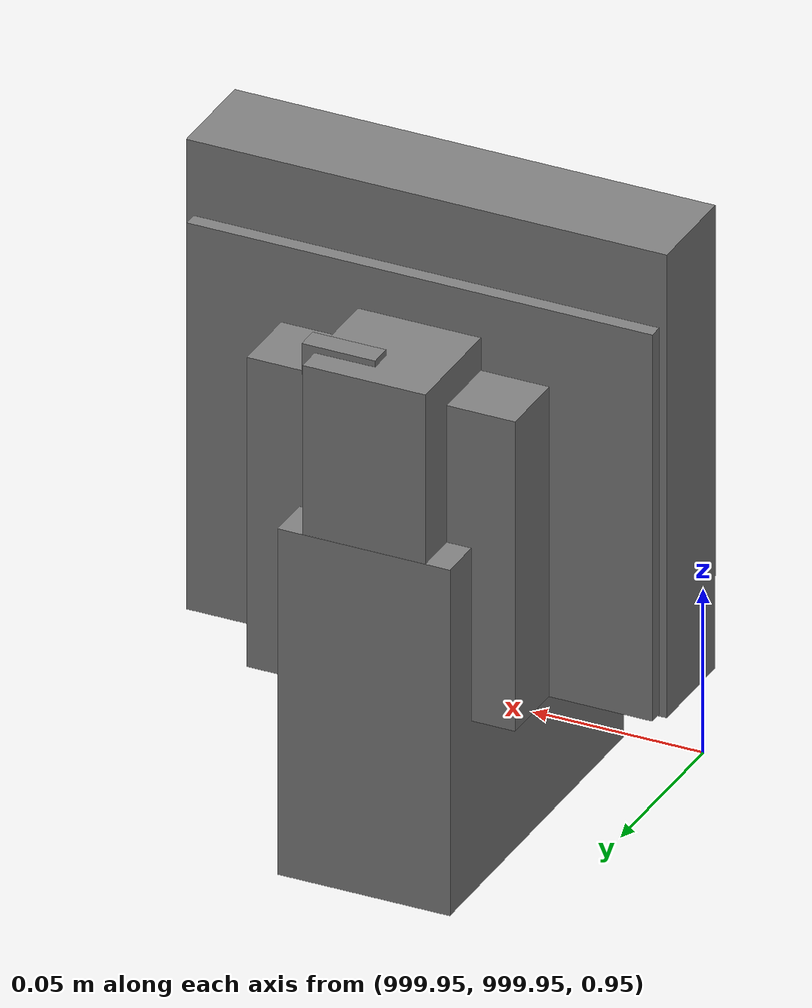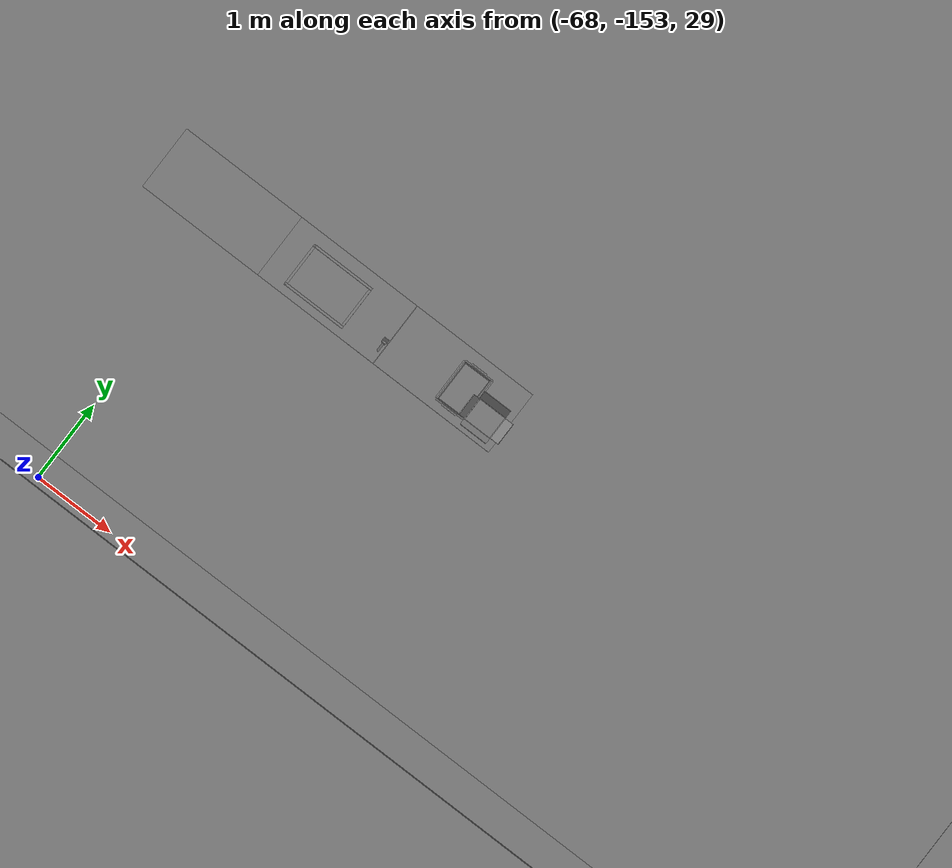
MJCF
<mujoco>
    <option gravity="0.000000000 0.000000000 -9.810000420" timestep="0.0049999999" integrator="implicitfast" density="1.225" viscosity="1.8000001e-05" noslip_iterations="10" iterations="100" sdf_iterations="50">
        <flag multiccd="disable"/>
    </option>
    <size memory="1000M"/>
    <compiler coordinate="local"/>
    <worldbody>
        <light cutoff="30" pos="0 1 1" dir="0 -1 -2"/>
        <light cutoff="30" pos="0 -1 1" dir="0 1 -2"/>
        <body pos="1000.000000000 1000.000000000 1.000000000" euler="0.000011953 0.000005123 -179.999984741" name="openloong_gripper_2f85_fix_base_usda_intel_box">
            <geom contype="1" conaffinity="1" density="1000" type="box" material="" rgba="0.500000000 0.500000000 0.500000000 1.000000000" solimp="0.899999976 0.949999988 0.001000000" friction="1.000000000 0.005000000 0.000100000" solref="0.020000000 1.000000000" margin="0" condim="3" group="0" pos="0.000000000 -0.000067139 0.000082284" quat="0.707106709 0.000000225 0.000000253 0.707106650" size="0.052800003 0.025300000 0.052800003" name="openloong_gripper_2f85_fix_base_usda_geom_8AC24F91_84A7_495A_9B0A_11FEA61C31B9"/>
            <freejoint name="openloong_gripper_2f85_fix_base_usda_intel_box_joint"/>
            <site size="0.005000000 0.005000000 0.005000000" rgba="0.500000000 0.500000000 0.500000000 1.000000000" pos="0.000000000 0.000000000 0.000000000" quat="0.999961913 0.008726500 0.000000000 0.000000000" group="0" type="sphere" name="openloong_gripper_2f85_fix_base_usda_intel_boxsite"/>
        </body>
        <body pos="1000.000000000 1000.000000000 1.000000000" euler="0.000000000 0.000000000 180.000000000" name="openloong_gripper_2f85_fix_base_usda_wifi_box">
            <geom contype="1" conaffinity="1" density="1000" type="box" material="" rgba="0.500000000 0.500000000 0.500000000 1.000000000" solimp="0.899999976 0.949999988 0.001000000" friction="1.000000000 0.005000000 0.000100000" solref="0.020000000 1.000000000" margin="0" condim="3" group="0" pos="0.000000000 0.000000000 0.058978677" quat="0.000000000 0.000000047 0.000000000 1.000000000" size="0.068499997 0.018999999 0.059000000" name="openloong_gripper_2f85_fix_base_usda_geom_F2FC9448_9647_4AB3_8355_FB96AB6B14C9"/>
            <freejoint name="openloong_gripper_2f85_fix_base_usda_wifi_box_joint"/>
            <site size="0.005000000 0.005000000 0.005000000" rgba="0.500000000 0.500000000 0.500000000 1.000000000" pos="0.000000000 0.000000000 0.000000000" quat="0.999961913 0.008726500 0.000000000 0.000000000" group="0" type="sphere" name="openloong_gripper_2f85_fix_base_usda_wifi_boxsite"/>
        </body>
        <body pos="-65.937789917 -149.021377563 31.163599014" euler="-159.558380127 -32.701610565 123.501167297" mocap="true" name="spotlight6_SpotLight"/>
        <body pos="1000.000000000 1000.000000000 1.000000000" euler="0.000000000 0.000000000 180.000000000" name="openloong_gripper_2f85_fix_base_usda_cpu_fan">
            <geom contype="1" conaffinity="1" density="1000" type="box" material="" rgba="0.500000000 0.500000000 0.500000000 1.000000000" solimp="0.899999976 0.949999988 0.001000000" friction="1.000000000 0.005000000 0.000100000" solref="0.020000000 1.000000000" margin="0" condim="3" group="0" pos="0.000000000 0.000000000 0.070034981" quat="0.000000000 0.000000000 0.000000000 1.000000000" size="0.070700005 0.014699999 0.070700005" name="openloong_gripper_2f85_fix_base_usda_geom_2E707CDB_8597_48AD_9A5F_AD43F95CF962"/>
            <freejoint name="openloong_gripper_2f85_fix_base_usda_cpu_fan_joint"/>
            <site size="0.005000000 0.005000000 0.005000000" rgba="0.500000000 0.500000000 0.500000000 1.000000000" pos="0.000000000 0.000000000 0.000000000" quat="0.999961913 0.008726535 0.000000000 0.000000000" group="0" type="sphere" name="openloong_gripper_2f85_fix_base_usda_cpu_fancsite"/>
        </body>
        <body pos="-66.069511414 -149.572708130 31.165668488" euler="161.270858765 5.213769436 134.511306763" mocap="true" name="spotlight5_SpotLight"/>
        <body pos="1000.000000000 999.999938965 1.000000000" euler="0.000000000 0.000000000 180.000000000" name="openloong_gripper_2f85_fix_base_usda_intelcore_i5">
            <geom contype="1" conaffinity="1" density="1000" type="box" material="" rgba="0.500000000 0.500000000 0.500000000 1.000000000" solimp="0.899999976 0.949999988 0.001000000" friction="1.000000000 0.005000000 0.000100000" solref="0.020000000 1.000000000" margin="0" condim="3" group="0" pos="0.000000000 0.000000000 0.051722717" quat="0.707106709 0.000000000 0.000000000 -0.707106769" size="0.052800000 0.018080002 0.052800000" name="openloong_gripper_2f85_fix_base_usda_geom_2104DFA7_9E84_4F8C_A78C_5410D04820B3"/>
            <freejoint name="openloong_gripper_2f85_fix_base_usda_intelcore_i5_joint"/>
            <site size="0.005000000 0.005000000 0.005000000" rgba="0.500000000 0.500000000 0.500000000 1.000000000" pos="0.000000000 0.000000000 0.000000000" quat="0.999961913 0.008726534 0.000000000 0.000000000" group="0" type="sphere" name="openloong_gripper_2f85_fix_base_usda_intelcore_i5site"/>
        </body>
        <body pos="-65.822265625 -149.332199097 31.168817520" euler="148.118743896 -52.623718262 -84.778762817" mocap="true" name="spotlight2_SpotLight"/>
        <body pos="1000.000000000 1000.000000000 1.000000000" euler="0.000000000 0.000000000 180.000000000" name="openloong_gripper_2f85_fix_base_usda_battery_01">
            <geom contype="1" conaffinity="1" density="1000" type="box" material="" rgba="0.500000000 0.500000000 0.500000000 1.000000000" solimp="0.899999976 0.949999988 0.001000000" friction="1.000000000 0.005000000 0.000100000" solref="0.020000000 1.000000000" margin="0" condim="3" group="0" pos="-0.011123657 -0.041940309 0.101691343" quat="1.000000000 0.000000000 0.000000000 0.000000000" size="0.010800000 0.003375000 0.004725000" name="openloong_gripper_2f85_fix_base_usda_geom_8AE44366_4F46_49AE_ACAF_534DD4073FE4"/>
            <geom contype="1" conaffinity="1" density="1000" type="box" material="" rgba="0.500000000 0.500000000 0.500000000 1.000000000" solimp="0.899999976 0.949999988 0.001000000" friction="1.000000000 0.005000000 0.000100000" solref="0.020000000 1.000000000" margin="0" condim="3" group="0" pos="-0.010876465 -0.044247437 0.047066893" quat="0.998702705 -0.050920475 0.000000000 0.000000000" size="0.009450001 0.002700000 0.024975000" name="openloong_gripper_2f85_fix_base_usda_geom_E0A31225_9040_4E91_8655_8E2AE9365793"/>
            <geom contype="1" conaffinity="1" density="1000" type="box" material="" rgba="0.500000000 0.500000000 0.500000000 1.000000000" solimp="0.899999976 0.949999988 0.001000000" friction="1.000000000 0.005000000 0.000100000" solref="0.020000000 1.000000000" margin="0" condim="3" group="0" pos="-0.001235962 -0.000659180 0.047381196" quat="1.000000000 0.000000000 0.000000000 0.000000000" size="0.039420001 0.039150000 0.047250003" name="openloong_gripper_2f85_fix_base_usda_geom_59E5E1DB_386B_4955_8086_493FCF5FB4A9"/>
            <geom contype="1" conaffinity="1" density="1000" type="box" material="" rgba="0.500000000 0.500000000 0.500000000 1.000000000" solimp="0.899999976 0.949999988 0.001000000" friction="1.000000000 0.005000000 0.000100000" solref="0.020000000 1.000000000" margin="0" condim="3" group="0" pos="-0.010876465 -0.039138794 0.009851727" quat="1.000000000 0.000000000 0.000000000 0.000000000" size="0.009450001 0.010800000 0.013500000" name="openloong_gripper_2f85_fix_base_usda_geom_CA9B58F6_412E_4F47_B90A_E1A70E683B42"/>
            <geom contype="1" conaffinity="1" density="1000" type="box" material="" rgba="0.500000000 0.500000000 0.500000000 1.000000000" solimp="0.899999976 0.949999988 0.001000000" friction="1.000000000 0.005000000 0.000100000" solref="0.020000000 1.000000000" margin="0" condim="3" group="0" pos="-0.010876465 -0.041528322 0.071508206" quat="1.000000000 0.000000000 0.000000000 0.000000000" size="0.009450001 0.002700000 0.027000001" name="openloong_gripper_2f85_fix_base_usda_geom_EE4B803A_61D9_4B77_84D5_D79793A89197"/>
            <freejoint name="openloong_gripper_2f85_fix_base_usda_battery_01_joint"/>
            <site size="0.005000000 0.005000000 0.005000000" rgba="0.500000000 0.500000000 0.500000000 1.000000000" pos="0.000000000 0.000000000 0.000000000" quat="0.999961913 0.008726500 0.000000000 0.000000000" group="0" type="sphere" name="openloong_gripper_2f85_fix_base_usda_battery_01site"/>
        </body>
        <body pos="-64.866622925 -149.383972168 30.183746338" euler="89.999984741 89.999946594 0.000000000" name="openloong_gripper_2f85_fix_base_usda_bluebox_01">
            <geom contype="1" conaffinity="1" density="1000" type="box" material="" rgba="0.500000000 0.500000000 0.500000000 1.000000000" solimp="0.899999976 0.949999988 0.001000000" friction="1.000000000 0.005000000 0.000100000" solref="0.020000000 1.000000000" margin="0" condim="3" group="0" pos="0.276580811 0.187225342 0.000068665" quat="0.707106948 0.000077471 0.707106352 0.000077486" size="0.100000001 0.057999998 0.010000000" name="openloong_gripper_2f85_fix_base_usda_geom_C87D8703_831E_4648_923F_B389B06707AD"/>
            <geom contype="1" conaffinity="1" density="1000" type="box" material="" rgba="0.500000000 0.500000000 0.500000000 1.000000000" solimp="0.899999976 0.949999988 0.001000000" friction="1.000000000 0.005000000 0.000100000" solref="0.020000000 1.000000000" margin="0" condim="3" group="0" pos="0.000000000 0.002883911 0.000000000" quat="0.999999881 0.000000000 0.000000000 0.000000000" size="0.254000008 0.003000000 0.172000006" name="openloong_gripper_2f85_fix_base_usda_geom_A713D02F_0E0E_4D93_9018_A7EEAA8C4270"/>
            <geom contype="1" conaffinity="1" density="1000" type="box" material="" rgba="0.500000000 0.500000000 0.500000000 1.000000000" solimp="0.899999976 0.949999988 0.001000000" friction="1.000000000 0.005000000 0.000100000" solref="0.020000000 1.000000000" margin="0" condim="3" group="0" pos="0.000000000 0.124874115 0.173484802" quat="0.999796331 0.020176515 -0.000000015 0.000000030" size="0.259999990 0.119999997 0.007000000" name="openloong_gripper_2f85_fix_base_usda_geom_C9259243_3F37_4791_8D67_2282705E539C"/>
            <geom contype="1" conaffinity="1" density="1000" type="box" material="" rgba="0.500000000 0.500000000 0.500000000 1.000000000" solimp="0.899999976 0.949999988 0.001000000" friction="1.000000000 0.005000000 0.000100000" solref="0.020000000 1.000000000" margin="0" condim="3" group="0" pos="0.000000000 0.124874115 -0.173469543" quat="0.999796331 -0.020176545 -0.000000015 0.000000000" size="0.259999990 0.119999997 0.007000000" name="openloong_gripper_2f85_fix_base_usda_geom_2E996234_26FF_466B_86E6_40550BA97F4E"/>
            <geom contype="1" conaffinity="1" density="1000" type="box" material="" rgba="0.500000000 0.500000000 0.500000000 1.000000000" solimp="0.899999976 0.949999988 0.001000000" friction="1.000000000 0.005000000 0.000100000" solref="0.020000000 1.000000000" margin="0" condim="3" group="0" pos="0.000000000 0.214008331 0.188980103" quat="0.999912977 0.013176724 0.000000015 0.000000000" size="0.259999990 0.029999999 0.012500000" name="openloong_gripper_2f85_fix_base_usda_geom_A75C3ADD_0A4E_478C_8154_A6EB6CA5FDBE"/>
            <geom contype="1" conaffinity="1" density="1000" type="box" material="" rgba="0.500000000 0.500000000 0.500000000 1.000000000" solimp="0.899999976 0.949999988 0.001000000" friction="1.000000000 0.005000000 0.000100000" solref="0.020000000 1.000000000" margin="0" condim="3" group="0" pos="-0.258361816 0.125289917 0.001876831" quat="0.702796936 -0.020792112 0.710783124 0.020769298" size="0.189999998 0.119999997 0.009000000" name="openloong_gripper_2f85_fix_base_usda_geom_3A7B55E3_FE9E_4C8C_8BA8_8024CA224DBE"/>
            <geom contype="1" conaffinity="1" density="1000" type="box" material="" rgba="0.500000000 0.500000000 0.500000000 1.000000000" solimp="0.899999976 0.949999988 0.001000000" friction="1.000000000 0.005000000 0.000100000" solref="0.020000000 1.000000000" margin="0" condim="3" group="0" pos="0.000000000 0.214008331 -0.188980103" quat="0.999912977 -0.013176769 0.000000030 0.000000015" size="0.259999990 0.029999999 0.012500000" name="openloong_gripper_2f85_fix_base_usda_geom_A22F4987_13AF_4A2E_A7D1_0AB0FDA8CB27"/>
            <geom contype="1" conaffinity="1" density="1000" type="box" material="" rgba="0.500000000 0.500000000 0.500000000 1.000000000" solimp="0.899999976 0.949999988 0.001000000" friction="1.000000000 0.005000000 0.000100000" solref="0.020000000 1.000000000" margin="0" condim="3" group="0" pos="-0.276611328 0.187225342 0.000068665" quat="0.707106650 0.000077441 0.707106709 0.000077456" size="0.100000001 0.057999998 0.010000000" name="openloong_gripper_2f85_fix_base_usda_geom_B75B9189_CFDC_46FD_9D40_81C07BE1E4E3"/>
            <geom contype="1" conaffinity="1" density="1000" type="box" material="" rgba="0.500000000 0.500000000 0.500000000 1.000000000" solimp="0.899999976 0.949999988 0.001000000" friction="1.000000000 0.005000000 0.000100000" solref="0.020000000 1.000000000" margin="0" condim="3" group="0" pos="0.258331299 0.125289917 0.001876831" quat="0.702851415 0.018856421 0.710823774 -0.019329369" size="0.189999998 0.119999997 0.009000000" name="openloong_gripper_2f85_fix_base_usda_geom_73CD29C4_44E1_4C4F_AB6C_24AE6915B605"/>
            <freejoint name="openloong_gripper_2f85_fix_base_usda_bluebox_01_joint"/>
            <site size="0.005000000 0.005000000 0.005000000" rgba="0.500000000 0.500000000 0.500000000 1.000000000" pos="0.000000000 0.000000000 0.000000000" quat="0.999961913 0.008726534 0.000000000 0.000000000" group="0" type="sphere" name="openloong_gripper_2f85_fix_base_usda_bluebox_01site"/>
        </body>
        <body pos="-64.496299744 -149.491867065 30.235729218" euler="0.000000000 0.000000000 89.999946594" name="openloong_gripper_2f85_fix_base_usda_cardboardbox_01">
            <geom contype="1" conaffinity="1" density="1000" type="box" material="" rgba="0.500000000 0.500000000 0.500000000 1.000000000" solimp="0.899999976 0.949999988 0.001000000" friction="1.000000000 0.005000000 0.000100000" solref="0.020000000 1.000000000" margin="0" condim="3" group="0" pos="-0.003166199 -0.004086494 0.005052090" quat="1.000000000 0.000000000 0.000000000 0.000000000" size="0.142499998 0.177500010 0.005000000" name="openloong_gripper_2f85_fix_base_usda_geom_0F6BE1C3_B931_42C3_AD66_848A49C80D14"/>
            <geom contype="1" conaffinity="1" density="1000" type="box" material="" rgba="0.500000000 0.500000000 0.500000000 1.000000000" solimp="0.899999976 0.949999988 0.001000000" friction="1.000000000 0.005000000 0.000100000" solref="0.020000000 1.000000000" margin="0" condim="3" group="0" pos="-0.003166199 0.170316696 0.150570869" quat="1.000000000 0.000000000 0.000000000 0.000000000" size="0.142499998 0.005000000 0.149999991" name="openloong_gripper_2f85_fix_base_usda_geom_171869A5_43BD_4FD0_BABE_CE106AC61CBC"/>
            <geom contype="1" conaffinity="1" density="1000" type="box" material="" rgba="0.500000000 0.500000000 0.500000000 1.000000000" solimp="0.899999976 0.949999988 0.001000000" friction="1.000000000 0.005000000 0.000100000" solref="0.020000000 1.000000000" margin="0" condim="3" group="0" pos="-0.147399902 -0.005307198 0.150570869" quat="1.000000000 0.000000000 0.000000000 0.000000000" size="0.005000000 0.177500010 0.149999991" name="openloong_gripper_2f85_fix_base_usda_geom_4A52A0D4_6305_4237_9575_70AD82183264"/>
            <geom contype="1" conaffinity="1" density="1000" type="box" material="" rgba="0.500000000 0.500000000 0.500000000 1.000000000" solimp="0.899999976 0.949999988 0.001000000" friction="1.000000000 0.005000000 0.000100000" solref="0.020000000 1.000000000" margin="0" condim="3" group="0" pos="0.140275955 -0.005307198 0.150570869" quat="1.000000000 0.000000000 0.000000000 0.000000000" size="0.005000000 0.177500010 0.149999991" name="openloong_gripper_2f85_fix_base_usda_geom_36D9EF6B_2486_472F_AC7A_95D79865A064"/>
            <geom contype="1" conaffinity="1" density="1000" type="box" material="" rgba="0.500000000 0.500000000 0.500000000 1.000000000" solimp="0.899999976 0.949999988 0.001000000" friction="1.000000000 0.005000000 0.000100000" solref="0.020000000 1.000000000" margin="0" condim="3" group="0" pos="-0.003166199 -0.181550980 0.150570869" quat="1.000000000 0.000000000 0.000000000 0.000000000" size="0.142499998 0.005000000 0.149999991" name="openloong_gripper_2f85_fix_base_usda_geom_3D722326_4821_40CE_BD5B_9F892F31AAC2"/>
            <freejoint name="openloong_gripper_2f85_fix_base_usda_cardboardbox_01_joint"/>
            <site size="0.005000000 0.005000000 0.005000000" rgba="0.500000000 0.500000000 0.500000000 1.000000000" pos="0.000000000 0.000000000 0.000000000" quat="0.999961913 0.008726535 0.000000000 0.000000000" group="0" type="sphere" name="openloong_gripper_2f85_fix_base_usda_site_24D6E2CE_0B4C_4CFA_ADFF_AAA5D82BD273"/>
            <body pos="0.139160156 -0.004048347 0.301930904" euler="-179.999954224 49.383502960 179.999954224" name="openloong_gripper_2f85_fix_base_usda_A1_006">
                <geom contype="1" conaffinity="1" density="1000" type="box" material="" rgba="0.500000000 0.500000000 0.500000000 1.000000000" solimp="0.899999976 0.949999988 0.001000000" friction="1.000000000 0.005000000 0.000100000" solref="0.020000000 1.000000000" margin="0" condim="3" group="0" pos="-0.071587563 0.000009537 0.001745224" quat="0.999999881 0.000000000 0.000000000 0.000000000" size="0.071249999 0.179999992 0.002500000" name="openloong_gripper_2f85_fix_base_usda_geom_C1A3AFFF_F81D_4297_A26C_425DEC69F7C5"/>
                <joint armature="0" stiffness="0.07" damping="0.0099999998" axis="0.000000 1.000000 0.000000" type="hinge" name="openloong_gripper_2f85_fix_base_usda_A1_006"/>
            </body>
            <body pos="-0.145902634 -0.004086494 0.301938057" euler="-180.000000000 -60.000011444 -180.000000000" name="openloong_gripper_2f85_fix_base_usda_A2_006">
                <geom contype="1" conaffinity="1" density="1000" type="box" material="" rgba="0.500000000 0.500000000 0.500000000 1.000000000" solimp="0.899999976 0.949999988 0.001000000" friction="1.000000000 0.005000000 0.000100000" solref="0.020000000 1.000000000" margin="0" condim="3" group="0" pos="0.071268082 0.000009537 0.002717972" quat="0.000002921 0.000000000 -0.000000030 0.999999881" size="0.071249999 0.179999992 0.002500000" name="openloong_gripper_2f85_fix_base_usda_geom_22073380_AFCF_40B1_BB10_CBC0731A2CAA"/>
                <joint armature="0" stiffness="0.07" damping="0.0099999998" axis="0.000000 1.000000 0.000000" type="hinge" name="openloong_gripper_2f85_fix_base_usda_A2_006"/>
            </body>
            <body pos="-0.003385544 0.175991058 0.301930904" euler="-125.858116150 -0.000004561 0.000002331" name="openloong_gripper_2f85_fix_base_usda_B2_006">
                <geom contype="1" conaffinity="1" density="1000" type="box" material="" rgba="0.500000000 0.500000000 0.500000000 1.000000000" solimp="0.899999976 0.949999988 0.001000000" friction="1.000000000 0.005000000 0.000100000" solref="0.020000000 1.000000000" margin="0" condim="3" group="0" pos="0.000009537 -0.070939064 -0.002470016" quat="0.999614120 0.027776197 -0.000000015 0.000000030" size="0.137500003 0.064999998 0.005000000" name="openloong_gripper_2f85_fix_base_usda_geom_BF641821_F10E_43D8_9AD6_4E638EB4A07F"/>
                <joint armature="0" stiffness="0.07" damping="0.0099999998" axis="1.000000 0.000000 0.000000" type="hinge" name="openloong_gripper_2f85_fix_base_usda_B2_006"/>
            </body>
            <body pos="-0.003385544 -0.184140205 0.301938057" euler="147.805557251 0.000000000 0.000000000" name="openloong_gripper_2f85_fix_base_usda_B1_006">
                <geom contype="1" conaffinity="1" density="1000" type="box" material="" rgba="0.500000000 0.500000000 0.500000000 1.000000000" solimp="0.899999976 0.949999988 0.001000000" friction="1.000000000 0.005000000 0.000100000" solref="0.020000000 1.000000000" margin="0" condim="3" group="0" pos="-0.000028610 0.070202351 -0.002703667" quat="0.999614179 -0.027776167 0.000000000 0.000000000" size="0.137500003 0.064999998 0.005000000" name="openloong_gripper_2f85_fix_base_usda_geom_E0483E14_C63E_4C95_B8F2_85CD405BBFF7"/>
                <joint armature="0" stiffness="0.07" damping="0.0099999998" axis="1.000000 0.000000 0.000000" type="hinge" name="openloong_gripper_2f85_fix_base_usda_B1_006"/>
            </body>
        </body>
        <body pos="-65.882858276 -149.481979370 30.229999542" euler="-64.487716675 0.000000000 0.000000000" name="openloong_gripper_2f85_fix_base_usda_Barcode">
            <geom contype="1" conaffinity="1" density="1000" type="box" material="" rgba="0.500000000 0.500000000 0.500000000 1.000000000" solimp="0.899999976 0.949999988 0.001000000" friction="1.000000000 0.005000000 0.000100000" solref="0.020000000 1.000000000" margin="0" condim="3" group="0" pos="0.000000000 0.013038635 0.001419067" quat="0.000000000 0.000000000 0.000000000 1.000000119" size="0.034000002 0.010000000 0.017999999" name="openloong_gripper_2f85_fix_base_usda_geom_2572DB17_6241_44FB_A3B3_C5426CB43957"/>
            <geom contype="1" conaffinity="1" density="1000" type="box" material="" rgba="0.500000000 0.500000000 0.500000000 1.000000000" solimp="0.899999976 0.949999988 0.001000000" friction="1.000000000 0.005000000 0.000100000" solref="0.020000000 1.000000000" margin="0" condim="3" group="0" pos="0.000000000 -0.035301208 -0.007095337" quat="0.000000000 0.000000000 -0.043619365 0.999048233" size="0.028999999 0.010000000 0.020000000" name="openloong_gripper_2f85_fix_base_usda_geom_DBCB8397_59B8_447C_AF71_EC77A1C13859"/>
            <geom contype="1" conaffinity="1" density="1000" type="box" material="" rgba="0.500000000 0.500000000 0.500000000 1.000000000" solimp="0.899999976 0.949999988 0.001000000" friction="1.000000000 0.005000000 0.000100000" solref="0.020000000 1.000000000" margin="0" condim="3" group="0" pos="0.000000000 -0.043411255 -0.011749268" quat="0.922262907 0.386563420 0.000000000 0.000000000" size="0.026000001 0.010000000 0.020000000" name="openloong_gripper_2f85_fix_base_usda_geom_77FAF851_22DB_47D8_9CD5_ADEFBF21B119"/>
            <geom contype="1" conaffinity="1" density="1000" type="box" material="" rgba="0.500000000 0.500000000 0.500000000 1.000000000" solimp="0.899999976 0.949999988 0.001000000" friction="1.000000000 0.005000000 0.000100000" solref="0.020000000 1.000000000" margin="0" condim="3" group="0" pos="0.000000000 -0.016967773 -0.031860352" quat="0.000000000 0.000000000 0.000000000 1.000000119" size="0.008000000 0.010000000 0.013000000" name="openloong_gripper_2f85_fix_base_usda_geom_992EFC88_B92B_40DC_8322_2A55436ADB36"/>
            <geom contype="1" conaffinity="1" density="1000" type="box" material="" rgba="0.500000000 0.500000000 0.500000000 1.000000000" solimp="0.899999976 0.949999988 0.001000000" friction="1.000000000 0.005000000 0.000100000" solref="0.020000000 1.000000000" margin="0" condim="3" group="0" pos="0.000000000 -0.001869202 0.000312805" quat="0.953716993 0.300705761 0.000000000 0.000000000" size="0.032000002 0.010000000 0.018999999" name="openloong_gripper_2f85_fix_base_usda_geom_42A9A8FF_D085_4465_A6B2_B816B93D570E"/>
            <geom contype="1" conaffinity="1" density="1000" type="box" material="" rgba="0.500000000 0.500000000 0.500000000 1.000000000" solimp="0.899999976 0.949999988 0.001000000" friction="1.000000000 0.005000000 0.000100000" solref="0.020000000 1.000000000" margin="0" condim="3" group="0" pos="0.000000000 -0.019531250 -0.003173828" quat="0.953716993 0.300705761 0.000000000 0.000000000" size="0.030999999 0.010000000 0.020000000" name="openloong_gripper_2f85_fix_base_usda_geom_4EDCC84F_7872_4DE2_9594_5C8D4C59E8AD"/>
            <geom contype="1" conaffinity="1" density="1000" type="box" material="" rgba="0.500000000 0.500000000 0.500000000 1.000000000" solimp="0.899999976 0.949999988 0.001000000" friction="1.000000000 0.005000000 0.000100000" solref="0.020000000 1.000000000" margin="0" condim="3" group="0" pos="0.000000000 -0.035301208 -0.007095337" quat="0.953716993 0.300705761 0.000000000 0.000000000" size="0.028999999 0.010000000 0.020000000" name="openloong_gripper_2f85_fix_base_usda_geom_3E557E97_9025_4643_9921_4A05416C0F69"/>
            <geom contype="1" conaffinity="1" density="1000" type="box" material="" rgba="0.500000000 0.500000000 0.500000000 1.000000000" solimp="0.899999976 0.949999988 0.001000000" friction="1.000000000 0.005000000 0.000100000" solref="0.020000000 1.000000000" margin="0" condim="3" group="0" pos="0.000000000 -0.042617798 -0.071121216" quat="0.000000000 0.000000000 0.000000000 1.000000119" size="0.013000000 0.021000000 0.059999999" name="openloong_gripper_2f85_fix_base_usda_geom_D7A6DAD6_9BB2_4DBC_9C43_79D6EF39426E"/>
            <freejoint name="openloong_gripper_2f85_fix_base_usda_Barcode_joint"/>
            <site size="0.005000000 0.005000000 0.005000000" rgba="0.500000000 0.500000000 0.500000000 1.000000000" pos="0.000000000 0.000000000 0.000000000" quat="1.000000000 0.000000000 0.000000000 0.000000000" group="0" type="sphere" name="openloong_gripper_2f85_fix_base_usda_Barcode_site"/>
        </body>
        <body pos="-66.745018005 -149.392349243 30.184000015" euler="0.000000000 0.000000000 89.999946594" name="[22333429889937]_Basket_01">
            <geom contype="1" conaffinity="1" density="1000" type="box" material="" rgba="0.500000000 0.500000000 0.500000000 1.000000000" solimp="0.899999976 0.949999988 0.001000000" friction="1.000000000 0.005000000 0.000100000" solref="0.020000000 1.000000000" margin="0" condim="3" group="0" pos="-0.052425385 0.389207840 0.089787483" quat="0.707107008 0.000000000 0.000000000 0.707106411" size="0.014249999 0.014249999 0.059999999" name="[22333429889937]_geom_CC768F8F_6E09_42CD_A6FB_BAA2885B1FDE"/>
            <geom contype="1" conaffinity="1" density="1000" type="box" material="" rgba="0.500000000 0.500000000 0.500000000 1.000000000" solimp="0.899999976 0.949999988 0.001000000" friction="1.000000000 0.005000000 0.000100000" solref="0.020000000 1.000000000" margin="0" condim="3" group="0" pos="0.264015198 -0.133043289 0.089787483" quat="0.707107008 0.000000000 0.000000000 0.707106411" size="0.014249999 0.014249999 0.059999999" name="[22333429889937]_geom_486401F3_8232_41FB_9914_ED15A0AB1809"/>
            <geom contype="1" conaffinity="1" density="1000" type="box" material="" rgba="0.500000000 0.500000000 0.500000000 1.000000000" solimp="0.899999976 0.949999988 0.001000000" friction="1.000000000 0.005000000 0.000100000" solref="0.020000000 1.000000000" margin="0" condim="3" group="0" pos="-0.264015198 -0.265548706 0.089793205" quat="0.707107008 0.000000000 0.000000000 0.707106411" size="0.014249999 0.014249999 0.059999999" name="[22333429889937]_geom_FF5D376A_3F80_4182_BF48_FE4D97C67FD5"/>
            <geom contype="1" conaffinity="1" density="1000" type="box" material="" rgba="0.500000000 0.500000000 0.500000000 1.000000000" solimp="0.899999976 0.949999988 0.001000000" friction="1.000000000 0.005000000 0.000100000" solref="0.020000000 1.000000000" margin="0" condim="3" group="0" pos="-0.160263062 -0.389322281 0.089793205" quat="0.707107008 0.000000000 0.000000000 0.707106411" size="0.014249999 0.014249999 0.059999999" name="[22333429889937]_geom_D08AA0C0_7F8F_4472_B8B0_D197F5A920AE"/>
            <geom contype="1" conaffinity="1" density="1000" type="box" material="" rgba="0.500000000 0.500000000 0.500000000 1.000000000" solimp="0.899999976 0.949999988 0.001000000" friction="1.000000000 0.005000000 0.000100000" solref="0.020000000 1.000000000" margin="0" condim="3" group="0" pos="0.162265778 -0.389322281 0.089787483" quat="0.707107008 0.000000000 0.000000000 0.707106411" size="0.014249999 0.014249999 0.059999999" name="[22333429889937]_geom_9FFFEA80_6AB1_41BB_9460_1B424294595A"/>
            <geom contype="1" conaffinity="1" density="1000" type="box" material="" rgba="0.500000000 0.500000000 0.500000000 1.000000000" solimp="0.899999976 0.949999988 0.001000000" friction="1.000000000 0.005000000 0.000100000" solref="0.020000000 1.000000000" margin="0" condim="3" group="0" pos="0.264015198 0.389207840 0.089787483" quat="0.707107008 0.000000000 0.000000000 0.707106411" size="0.014249999 0.014249999 0.059999999" name="[22333429889937]_geom_7DA8F236_8546_4447_BF82_06B2FC18FC51"/>
            <geom contype="1" conaffinity="1" density="1000" type="box" material="" rgba="0.500000000 0.500000000 0.500000000 1.000000000" solimp="0.899999976 0.949999988 0.001000000" friction="1.000000000 0.005000000 0.000100000" solref="0.020000000 1.000000000" margin="0" condim="3" group="0" pos="-0.264015198 -0.133043289 0.089793205" quat="0.707107008 0.000000000 0.000000000 0.707106411" size="0.014249999 0.014249999 0.059999999" name="[22333429889937]_geom_6BC96C41_38CA_4762_A472_2A32EFDEE1DD"/>
            <geom contype="1" conaffinity="1" density="1000" type="box" material="" rgba="0.500000000 0.500000000 0.500000000 1.000000000" solimp="0.899999976 0.949999988 0.001000000" friction="1.000000000 0.005000000 0.000100000" solref="0.020000000 1.000000000" margin="0" condim="3" group="0" pos="-0.264026642 0.269256592 0.089793205" quat="0.707107008 0.000000000 0.000000000 0.707106411" size="0.014249999 0.014249999 0.059999999" name="[22333429889937]_geom_8E7F7820_8F03_4016_A4E5_A8FC945DD0B4"/>
            <geom contype="1" conaffinity="1" density="1000" type="box" material="" rgba="0.500000000 0.500000000 0.500000000 1.000000000" solimp="0.899999976 0.949999988 0.001000000" friction="1.000000000 0.005000000 0.000100000" solref="0.020000000 1.000000000" margin="0" condim="3" group="0" pos="0.054462433 0.389207840 0.089787483" quat="0.707107008 0.000000000 0.000000000 0.707106411" size="0.014249999 0.014249999 0.059999999" name="[22333429889937]_geom_40C9A10B_87F1_4330_B42F_95FC9E61BECE"/>
            <geom contype="1" conaffinity="1" density="1000" type="box" material="" rgba="0.500000000 0.500000000 0.500000000 1.000000000" solimp="0.899999976 0.949999988 0.001000000" friction="1.000000000 0.005000000 0.000100000" solref="0.020000000 1.000000000" margin="0" condim="3" group="0" pos="0.054462433 -0.389322281 0.089787483" quat="0.707107008 0.000000000 0.000000000 0.707106411" size="0.014249999 0.014249999 0.059999999" name="[22333429889937]_geom_82577379_05FC_43B3_B540_1C4CCD68863C"/>
            <geom contype="1" conaffinity="1" density="1000" type="box" material="" rgba="0.500000000 0.500000000 0.500000000 1.000000000" solimp="0.899999976 0.949999988 0.001000000" friction="1.000000000 0.005000000 0.000100000" solref="0.020000000 1.000000000" margin="0" condim="3" group="0" pos="0.264015198 0.269256592 0.089793205" quat="0.707107008 0.000000000 0.000000000 0.707106411" size="0.014249999 0.014249999 0.059999999" name="[22333429889937]_geom_B8F8ADD4_ECF1_4309_94AC_1FB87AC1CC6E"/>
            <geom contype="1" conaffinity="1" density="1000" type="box" material="" rgba="0.500000000 0.500000000 0.500000000 1.000000000" solimp="0.899999976 0.949999988 0.001000000" friction="1.000000000 0.005000000 0.000100000" solref="0.020000000 1.000000000" margin="0" condim="3" group="0" pos="0.264015198 -0.389322281 0.089787483" quat="0.707107008 0.000000000 0.000000000 0.707106411" size="0.014249999 0.014249999 0.059999999" name="[22333429889937]_geom_0C089761_F94A_4089_96F3_CDEC62B99626"/>
            <geom contype="1" conaffinity="1" density="1000" type="box" material="" rgba="0.500000000 0.500000000 0.500000000 1.000000000" solimp="0.899999976 0.949999988 0.001000000" friction="1.000000000 0.005000000 0.000100000" solref="0.020000000 1.000000000" margin="0" condim="3" group="0" pos="0.000000000 0.000000000 0.015998840" quat="0.707107008 0.000000000 0.000000000 0.707106411" size="0.403499991 0.279000014 0.015750000" name="[22333429889937]_geom_B8959D7C_DB22_4D8F_A0B3_D496FF5B3042"/>
            <geom contype="1" conaffinity="1" density="1000" type="box" material="" rgba="0.500000000 0.500000000 0.500000000 1.000000000" solimp="0.899999976 0.949999988 0.001000000" friction="1.000000000 0.005000000 0.000100000" solref="0.020000000 1.000000000" margin="0" condim="3" group="0" pos="0.000000000 -0.389476776 0.163619041" quat="0.707107008 0.000000000 0.000000000 0.707106411" size="0.015000000 0.277500004 0.015750000" name="[22333429889937]_geom_95B72523_52D8_4CF4_839A_2B1F549D27ED"/>
            <geom contype="1" conaffinity="1" density="1000" type="box" material="" rgba="0.500000000 0.500000000 0.500000000 1.000000000" solimp="0.899999976 0.949999988 0.001000000" friction="1.000000000 0.005000000 0.000100000" solref="0.020000000 1.000000000" margin="0" condim="3" group="0" pos="0.162265778 0.389207840 0.089787483" quat="0.707107008 0.000000000 0.000000000 0.707106411" size="0.014249999 0.014249999 0.059999999" name="[22333429889937]_geom_C5D73BA3_A257_4DDC_88FF_3B289E892E6B"/>
            <geom contype="1" conaffinity="1" density="1000" type="box" material="" rgba="0.500000000 0.500000000 0.500000000 1.000000000" solimp="0.899999976 0.949999988 0.001000000" friction="1.000000000 0.005000000 0.000100000" solref="0.020000000 1.000000000" margin="0" condim="3" group="0" pos="0.000000000 0.389471054 0.163619041" quat="0.707107008 0.000000000 0.000000000 0.707106411" size="0.015000000 0.277500004 0.015750000" name="[22333429889937]_geom_8FF7C8C5_4F77_4084_8A29_D5A57039DD97"/>
            <geom contype="1" conaffinity="1" density="1000" type="box" material="" rgba="0.500000000 0.500000000 0.500000000 1.000000000" solimp="0.899999976 0.949999988 0.001000000" friction="1.000000000 0.005000000 0.000100000" solref="0.020000000 1.000000000" margin="0" condim="3" group="0" pos="-0.263511658 0.000000000 0.163619041" quat="0.707107008 0.000000000 0.000000000 0.707106411" size="0.403499991 0.015000000 0.015750000" name="[22333429889937]_geom_0642F962_FA7B_46A7_BFE9_ABB9CE242F79"/>
            <geom contype="1" conaffinity="1" density="1000" type="box" material="" rgba="0.500000000 0.500000000 0.500000000 1.000000000" solimp="0.899999976 0.949999988 0.001000000" friction="1.000000000 0.005000000 0.000100000" solref="0.020000000 1.000000000" margin="0" condim="3" group="0" pos="-0.264015198 0.141334534 0.089793205" quat="0.707107008 0.000000000 0.000000000 0.707106411" size="0.014249999 0.014249999 0.059999999" name="[22333429889937]_geom_64DF353E_B96D_4CF3_B699_384DAD3CCA93"/>
            <geom contype="1" conaffinity="1" density="1000" type="box" material="" rgba="0.500000000 0.500000000 0.500000000 1.000000000" solimp="0.899999976 0.949999988 0.001000000" friction="1.000000000 0.005000000 0.000100000" solref="0.020000000 1.000000000" margin="0" condim="3" group="0" pos="0.264015198 -0.265548706 0.089787483" quat="0.707107008 0.000000000 0.000000000 0.707106411" size="0.014249999 0.014249999 0.059999999" name="[22333429889937]_geom_B5967BAA_5CB0_4841_9F80_777C08938669"/>
            <geom contype="1" conaffinity="1" density="1000" type="box" material="" rgba="0.500000000 0.500000000 0.500000000 1.000000000" solimp="0.899999976 0.949999988 0.001000000" friction="1.000000000 0.005000000 0.000100000" solref="0.020000000 1.000000000" margin="0" condim="3" group="0" pos="-0.160263062 0.389207840 0.089787483" quat="0.707107008 0.000000000 0.000000000 0.707106411" size="0.014249999 0.014249999 0.059999999" name="[22333429889937]_geom_36AD639C_0BDB_4334_90D2_5C50E1DC8950"/>
            <geom contype="1" conaffinity="1" density="1000" type="box" material="" rgba="0.500000000 0.500000000 0.500000000 1.000000000" solimp="0.899999976 0.949999988 0.001000000" friction="1.000000000 0.005000000 0.000100000" solref="0.020000000 1.000000000" margin="0" condim="3" group="0" pos="-0.052425385 -0.389322281 0.089787483" quat="0.707107008 0.000000000 0.000000000 0.707106411" size="0.014249999 0.014249999 0.059999999" name="[22333429889937]_geom_A4A4DA74_2967_4A4C_91DC_3FEE0AEC3720"/>
            <geom contype="1" conaffinity="1" density="1000" type="box" material="" rgba="0.500000000 0.500000000 0.500000000 1.000000000" solimp="0.899999976 0.949999988 0.001000000" friction="1.000000000 0.005000000 0.000100000" solref="0.020000000 1.000000000" margin="0" condim="3" group="0" pos="-0.264026642 -0.389322281 0.089793205" quat="0.707107008 0.000000000 0.000000000 0.707106411" size="0.014249999 0.014249999 0.059999999" name="[22333429889937]_geom_05F9BAE6_1D14_494F_876F_6D9495DB0F6C"/>
            <geom contype="1" conaffinity="1" density="1000" type="box" material="" rgba="0.500000000 0.500000000 0.500000000 1.000000000" solimp="0.899999976 0.949999988 0.001000000" friction="1.000000000 0.005000000 0.000100000" solref="0.020000000 1.000000000" margin="0" condim="3" group="0" pos="0.264015198 0.141334534 0.089787483" quat="0.707107008 0.000000000 0.000000000 0.707106411" size="0.014249999 0.014249999 0.059999999" name="[22333429889937]_geom_B127A6A8_F684_4DB3_B2A6_47387DE99B94"/>
            <geom contype="1" conaffinity="1" density="1000" type="box" material="" rgba="0.500000000 0.500000000 0.500000000 1.000000000" solimp="0.899999976 0.949999988 0.001000000" friction="1.000000000 0.005000000 0.000100000" solref="0.020000000 1.000000000" margin="0" condim="3" group="0" pos="-0.264015198 0.389207840 0.089793205" quat="0.707107008 0.000000000 0.000000000 0.707106411" size="0.014249999 0.014249999 0.059999999" name="[22333429889937]_geom_9D65AC6E_A510_473B_9245_BBFC0FAD398F"/>
            <geom contype="1" conaffinity="1" density="1000" type="box" material="" rgba="0.500000000 0.500000000 0.500000000 1.000000000" solimp="0.899999976 0.949999988 0.001000000" friction="1.000000000 0.005000000 0.000100000" solref="0.020000000 1.000000000" margin="0" condim="3" group="0" pos="0.264015198 0.004480362 0.089787483" quat="0.707107008 0.000000000 0.000000000 0.707106411" size="0.014249999 0.014249999 0.059999999" name="[22333429889937]_geom_07556933_32B3_4CF6_99BD_F1707BC6F31F"/>
            <geom contype="1" conaffinity="1" density="1000" type="box" material="" rgba="0.500000000 0.500000000 0.500000000 1.000000000" solimp="0.899999976 0.949999988 0.001000000" friction="1.000000000 0.005000000 0.000100000" solref="0.020000000 1.000000000" margin="0" condim="3" group="0" pos="0.263694763 -0.000011444 0.163619041" quat="0.707107008 0.000000000 0.000000000 0.707106411" size="0.403499991 0.015000000 0.015750000" name="[22333429889937]_geom_E2D6B75F_7F5D_4A14_89D9_55840B8C5F03"/>
            <geom contype="1" conaffinity="1" density="1000" type="box" material="" rgba="0.500000000 0.500000000 0.500000000 1.000000000" solimp="0.899999976 0.949999988 0.001000000" friction="1.000000000 0.005000000 0.000100000" solref="0.020000000 1.000000000" margin="0" condim="3" group="0" pos="-0.264015198 0.004480362 0.089793205" quat="0.707107008 0.000000000 0.000000000 0.707106411" size="0.014249999 0.014249999 0.059999999" name="[22333429889937]_geom_DB66BC5B_0588_412C_B0F0_9766BC13F48C"/>
            <freejoint name="[22333429889937]_joint_76E02A61_B492_4A6F_AA13_334D8BA37F28"/>
        </body>
        <body pos="0.000000000 0.000000000 0.000000000" euler="0.000000000 0.000000000 0.000000000" name="Static Objects_Static Objects">
            <geom contype="1" conaffinity="1" density="1000" type="box" material="" rgba="0.500000000 0.500000000 0.500000000 1.000000000" solimp="0.899999976 0.949999988 0.001000000" friction="1.000000000 0.005000000 0.000100000" solref="0.020000000 1.000000000" margin="0" condim="3" group="0" pos="-67.544113159 -149.365814209 29.727830887" quat="0.500000417 0.499999970 0.499999553 0.499999970" size="0.381000012 0.319999993 0.041000001" name="Static Objects_geom_51F59E6E_8600_40E5_916E_F09BDD639E0E"/>
            <geom contype="1" conaffinity="1" density="1000" type="box" material="" rgba="0.500000000 0.500000000 0.500000000 1.000000000" solimp="0.899999976 0.949999988 0.001000000" friction="1.000000000 0.005000000 0.000100000" solref="0.020000000 1.000000000" margin="0" condim="3" group="0" pos="-68.239501953 -149.365814209 30.086868286" quat="0.500000417 0.499999970 0.499999553 0.499999970" size="0.370999992 0.039500002 0.745000005" name="Static Objects_geom_D3D811CF_2436_4B6B_8CCD_E69A7832C897"/>
            <geom contype="1" conaffinity="1" density="1000" type="box" material="" rgba="0.500000000 0.500000000 0.500000000 1.000000000" solimp="0.899999976 0.949999988 0.001000000" friction="1.000000000 0.005000000 0.000100000" solref="0.020000000 1.000000000" margin="0" condim="3" group="0" pos="-68.239501953 -149.365814209 30.147235870" quat="0.500000417 0.499999970 0.499999553 0.499999970" size="0.400000006 0.022000000 0.800000012" name="Static Objects_geom_1ECAF019_C5E3_49FE_8EA4_1C4B5454ED95"/>
            <geom contype="1" conaffinity="1" density="1000" type="box" material="" rgba="0.500000000 0.500000000 0.500000000 1.000000000" solimp="0.899999976 0.949999988 0.001000000" friction="1.000000000 0.005000000 0.000100000" solref="0.020000000 1.000000000" margin="0" condim="3" group="0" pos="-68.934890747 -149.365814209 29.727830887" quat="0.500000417 0.499999970 0.499999553 0.499999970" size="0.381000012 0.319999993 0.041000001" name="Static Objects_geom_4D8B48D4_FDE8_4021_99A9_D38599E41FD9"/>
            <geom contype="1" conaffinity="1" density="1000" type="box" material="" rgba="0.500000000 0.500000000 0.500000000 1.000000000" solimp="0.899999976 0.949999988 0.001000000" friction="1.000000000 0.005000000 0.000100000" solref="0.020000000 1.000000000" margin="0" condim="3" group="0" pos="-68.239501953 -149.365814209 29.561563492" quat="0.500000417 0.499999970 0.499999553 0.499999970" size="0.020000000 0.022000000 0.660000026" name="Static Objects_geom_3D5229DD_DE5D_41A4_932E_CADE66849DE9"/>
            <geom contype="1" conaffinity="1" density="1000" type="box" material="" rgba="0.500000000 0.500000000 0.500000000 1.000000000" solimp="0.899999976 0.949999988 0.001000000" friction="1.000000000 0.005000000 0.000100000" solref="0.020000000 1.000000000" margin="0" condim="3" group="0" pos="-65.945671082 -149.365814209 29.727830887" quat="0.500000417 0.499999970 0.499999553 0.499999970" size="0.381000012 0.319999993 0.041000001" name="Static Objects_geom_C72E4836_7748_4ACE_925F_09AFB2C51EA6"/>
            <geom contype="1" conaffinity="1" density="1000" type="box" material="" rgba="0.500000000 0.500000000 0.500000000 1.000000000" solimp="0.899999976 0.949999988 0.001000000" friction="1.000000000 0.005000000 0.000100000" solref="0.020000000 1.000000000" margin="0" condim="3" group="0" pos="-66.641059875 -149.365814209 30.086868286" quat="0.500000417 0.499999970 0.499999553 0.499999970" size="0.370999992 0.039500002 0.745000005" name="Static Objects_geom_246A740B_D54E_4DC2_AECE_42E7AE782F0F"/>
            <geom contype="1" conaffinity="1" density="1000" type="box" material="" rgba="0.500000000 0.500000000 0.500000000 1.000000000" solimp="0.899999976 0.949999988 0.001000000" friction="1.000000000 0.005000000 0.000100000" solref="0.020000000 1.000000000" margin="0" condim="3" group="0" pos="-66.641059875 -149.365814209 30.147235870" quat="0.500000417 0.499999970 0.499999553 0.499999970" size="0.400000006 0.022000000 0.800000012" name="Static Objects_geom_11AF9202_F1CC_4F26_ABFC_B2B935FEF827"/>
            <geom contype="1" conaffinity="1" density="1000" type="box" material="" rgba="0.500000000 0.500000000 0.500000000 1.000000000" solimp="0.899999976 0.949999988 0.001000000" friction="1.000000000 0.005000000 0.000100000" solref="0.020000000 1.000000000" margin="0" condim="3" group="0" pos="-67.336448669 -149.365814209 29.727830887" quat="0.500000417 0.499999970 0.499999553 0.499999970" size="0.381000012 0.319999993 0.041000001" name="Static Objects_geom_9B19344C_0EF0_4A66_978F_D37223DD5657"/>
            <geom contype="1" conaffinity="1" density="1000" type="box" material="" rgba="0.500000000 0.500000000 0.500000000 1.000000000" solimp="0.899999976 0.949999988 0.001000000" friction="1.000000000 0.005000000 0.000100000" solref="0.020000000 1.000000000" margin="0" condim="3" group="0" pos="-66.641059875 -149.365814209 29.561563492" quat="0.500000417 0.499999970 0.499999553 0.499999970" size="0.020000000 0.022000000 0.660000026" name="Static Objects_geom_B529A3D3_6038_40BF_9654_C125E077C1E8"/>
            <geom contype="1" conaffinity="1" density="1000" type="box" material="" rgba="0.500000000 0.500000000 0.500000000 1.000000000" solimp="0.899999976 0.949999988 0.001000000" friction="1.000000000 0.005000000 0.000100000" solref="0.020000000 1.000000000" margin="0" condim="3" group="0" pos="-64.338577271 -149.365814209 29.727830887" quat="0.500000417 0.499999970 0.499999553 0.499999970" size="0.381000012 0.319999993 0.041000001" name="Static Objects_geom_7607C62A_835A_47F5_9A88_D3BBCB4D79E6"/>
            <geom contype="1" conaffinity="1" density="1000" type="box" material="" rgba="0.500000000 0.500000000 0.500000000 1.000000000" solimp="0.899999976 0.949999988 0.001000000" friction="1.000000000 0.005000000 0.000100000" solref="0.020000000 1.000000000" margin="0" condim="3" group="0" pos="-65.033966064 -149.365814209 30.086868286" quat="0.500000417 0.499999970 0.499999553 0.499999970" size="0.370999992 0.039500002 0.745000005" name="Static Objects_geom_CCBC132D_C7B1_47FC_AC30_94FEA9211D58"/>
            <geom contype="1" conaffinity="1" density="1000" type="box" material="" rgba="0.500000000 0.500000000 0.500000000 1.000000000" solimp="0.899999976 0.949999988 0.001000000" friction="1.000000000 0.005000000 0.000100000" solref="0.020000000 1.000000000" margin="0" condim="3" group="0" pos="-65.033966064 -149.365814209 30.147235870" quat="0.500000417 0.499999970 0.499999553 0.499999970" size="0.400000006 0.022000000 0.800000012" name="Static Objects_geom_81339625_BF72_4DAF_8F37_0BB31845C91D"/>
            <geom contype="1" conaffinity="1" density="1000" type="box" material="" rgba="0.500000000 0.500000000 0.500000000 1.000000000" solimp="0.899999976 0.949999988 0.001000000" friction="1.000000000 0.005000000 0.000100000" solref="0.020000000 1.000000000" margin="0" condim="3" group="0" pos="-65.729354858 -149.365814209 29.727830887" quat="0.500000417 0.499999970 0.499999553 0.499999970" size="0.381000012 0.319999993 0.041000001" name="Static Objects_geom_F3264E3E_DE87_4831_91C1_A842E7072DD4"/>
            <geom contype="1" conaffinity="1" density="1000" type="box" material="" rgba="0.500000000 0.500000000 0.500000000 1.000000000" solimp="0.899999976 0.949999988 0.001000000" friction="1.000000000 0.005000000 0.000100000" solref="0.020000000 1.000000000" margin="0" condim="3" group="0" pos="-65.033966064 -149.365814209 29.561563492" quat="0.500000417 0.499999970 0.499999553 0.499999970" size="0.020000000 0.022000000 0.660000026" name="Static Objects_geom_1CE39791_8379_4F05_B727_7271990DD0FE"/>
            <geom contype="1" conaffinity="1" density="1000" type="box" material="" rgba="0.500000000 0.500000000 0.500000000 1.000000000" solimp="0.899999976 0.949999988 0.001000000" friction="1.000000000 0.005000000 0.000100000" solref="0.020000000 1.000000000" margin="0" condim="3" group="0" pos="-61.754566193 -137.853729248 33.906845093" quat="0.707107067 0.000000000 0.000000000 0.707106471" size="0.759999990 0.759999990 4.500000000" name="Static Objects_geom_6E0C1DC4_BAC9_4AA8_B251_4E6265C03FDD"/>
            <geom contype="1" conaffinity="1" density="1000" type="box" material="" rgba="0.500000000 0.500000000 0.500000000 1.000000000" solimp="0.899999976 0.949999988 0.001000000" friction="1.000000000 0.005000000 0.000100000" solref="0.020000000 1.000000000" margin="0" condim="3" group="0" pos="-57.511135101 -144.927108765 31.707921982" quat="1.000000000 0.000000000 0.000000000 0.000000000" size="0.200000003 8.000000000 2.299999952" name="Static Objects_geom_34264E91_29B7_4009_9FA0_3AD6C825CA8A"/>
            <geom contype="1" conaffinity="1" density="1000" type="box" material="" rgba="0.500000000 0.500000000 0.500000000 1.000000000" solimp="0.899999976 0.949999988 0.001000000" friction="1.000000000 0.005000000 0.000100000" solref="0.020000000 1.000000000" margin="0" condim="3" group="0" pos="-80.517646790 -157.574050903 31.688196182" quat="0.707107067 0.000000000 0.000000000 0.707106471" size="0.600000024 0.600000024 2.299999952" name="Static Objects_geom_739F6FBC_F21D_47F7_B677_D1C042D439F1"/>
            <geom contype="1" conaffinity="1" density="1000" type="box" material="" rgba="0.500000000 0.500000000 0.500000000 1.000000000" solimp="0.899999976 0.949999988 0.001000000" friction="1.000000000 0.005000000 0.000100000" solref="0.020000000 1.000000000" margin="0" condim="3" group="0" pos="-80.711044312 -147.414932251 31.666158676" quat="1.000000000 0.000000000 0.000000000 0.000000000" size="0.200000003 10.000000000 2.299999952" name="Static Objects_geom_72FD3BF5_125B_494B_BC3E_B1EDDD1859A9"/>
            <geom contype="1" conaffinity="1" density="1000" type="box" material="" rgba="0.500000000 0.500000000 0.500000000 1.000000000" solimp="0.899999976 0.949999988 0.001000000" friction="1.000000000 0.005000000 0.000100000" solref="0.020000000 1.000000000" margin="0" condim="3" group="0" pos="-57.687217712 -137.434692383 31.688196182" quat="0.707107067 0.000000000 0.000000000 0.707106471" size="0.600000024 0.600000024 2.299999952" name="Static Objects_geom_404971E1_4633_43B2_AD8B_90413806CDE1"/>
            <geom contype="1" conaffinity="1" density="1000" type="box" material="" rgba="0.500000000 0.500000000 0.500000000 1.000000000" solimp="0.899999976 0.949999988 0.001000000" friction="1.000000000 0.005000000 0.000100000" solref="0.020000000 1.000000000" margin="0" condim="3" group="0" pos="-69.537033081 -140.263229370 31.714921951" quat="0.707107067 0.000000000 0.000000000 0.707106471" size="0.759999990 4.500000000 2.299999952" name="Static Objects_geom_8B728F1C_1077_446E_8EA5_077677AD29CB"/>
            <geom contype="1" conaffinity="1" density="1000" type="box" material="" rgba="0.500000000 0.500000000 0.500000000 1.000000000" solimp="0.899999976 0.949999988 0.001000000" friction="1.000000000 0.005000000 0.000100000" solref="0.020000000 1.000000000" margin="0" condim="3" group="0" pos="-80.073638916 -137.853713989 33.906845093" quat="0.707107067 0.000000000 0.000000000 0.707106471" size="0.759999990 0.759999990 4.500000000" name="Static Objects_geom_5D12E0A8_9249_4099_B6CF_13D9819EF866"/>
            <geom contype="1" conaffinity="1" density="1000" type="box" material="" rgba="0.500000000 0.500000000 0.500000000 1.000000000" solimp="0.899999976 0.949999988 0.001000000" friction="1.000000000 0.005000000 0.000100000" solref="0.020000000 1.000000000" margin="0" condim="3" group="0" pos="-73.406707764 -155.734664917 31.707921982" quat="1.000000000 0.000000000 0.000000000 0.000000000" size="0.200000003 3.000000000 2.299999952" name="Static Objects_geom_DAE3D5B7_90D0_4B03_A1D9_9710E156F206"/>
            <geom contype="1" conaffinity="1" density="1000" type="box" material="" rgba="0.500000000 0.500000000 0.500000000 1.000000000" solimp="0.899999976 0.949999988 0.001000000" friction="1.000000000 0.005000000 0.000100000" solref="0.020000000 1.000000000" margin="0" condim="3" group="0" pos="-68.497543335 -137.448257446 31.707921982" quat="0.707107067 0.000000000 0.000000000 0.707106471" size="0.200000003 14.000000000 2.299999952" name="Static Objects_geom_FF5D1D89_D8ED_4D82_B87A_0057EABB4985"/>
            <geom contype="1" conaffinity="1" density="1000" type="cylinder" material="" rgba="0.500000000 0.500000000 0.500000000 1.000000000" solimp="0.899999976 0.949999988 0.001000000" friction="1.000000000 0.005000000 0.000100000" solref="0.020000000 1.000000000" margin="0" condim="3" group="0" pos="-68.868522644 -142.134506226 31.711090088" quat="0.707107067 0.000000000 0.000000000 0.707106471" size="0.509999990 2.299999952 1.000000000" name="Static Objects_geom_893DFAB0_195A_4179_A03E_77D9463BC762"/>
            <geom contype="1" conaffinity="1" density="1000" type="plane" material="" rgba="0.500000000 0.500000000 0.500000000 1.000000000" solimp="0.899999976 0.949999988 0.001000000" friction="1.000000000 0.005000000 0.000100000" solref="0.020000000 1.000000000" margin="0" condim="3" group="0" pos="-72.873703003 -147.131927490 29.409669876" quat="1.000000000 0.000000000 0.000000000 0.000000000" size="18.000000000 14.000000000 1.000000000" name="Static Objects_geom_3BE39069_1C9C_4ACE_9016_828A8C7E5C9E"/>
            <geom contype="1" conaffinity="1" density="1000" type="box" material="" rgba="0.500000000 0.500000000 0.500000000 1.000000000" solimp="0.899999976 0.949999988 0.001000000" friction="1.000000000 0.005000000 0.000100000" solref="0.020000000 1.000000000" margin="0" condim="3" group="0" pos="-79.943580627 -157.782272339 31.707921982" quat="0.707107067 0.000000000 0.000000000 0.707106471" size="0.200000003 7.000000000 2.299999952" name="Static Objects_geom_74BFC911_B17D_4683_AE2D_F2DA8D3084A7"/>
            <geom contype="1" conaffinity="1" density="1000" type="box" material="" rgba="0.500000000 0.500000000 0.500000000 1.000000000" solimp="0.899999976 0.949999988 0.001000000" friction="1.000000000 0.005000000 0.000100000" solref="0.020000000 1.000000000" margin="0" condim="3" group="0" pos="-65.421028137 -152.903442383 31.707921982" quat="0.707107067 0.000000000 0.000000000 0.707106471" size="0.200000003 7.800000191 2.299999952" name="Static Objects_geom_489D8A2E_6B2C_424C_8392_6384B4CEF722"/>
            <geom contype="1" conaffinity="1" density="1000" type="box" material="" rgba="0.500000000 0.500000000 0.500000000 1.000000000" solimp="0.899999976 0.949999988 0.001000000" friction="1.000000000 0.005000000 0.000100000" solref="0.020000000 1.000000000" margin="0" condim="3" group="0" pos="-74.776908875 -149.964416504 31.688196182" quat="1.000000000 0.000000000 0.000000000 0.000000000" size="0.600000024 0.409999996 2.299999952" name="Static Objects_geom_0E47DA45_7754_462D_8F44_274322B4BAE1"/>
            <geom contype="1" conaffinity="1" density="1000" type="cylinder" material="" rgba="0.500000000 0.500000000 0.500000000 1.000000000" solimp="0.899999976 0.949999988 0.001000000" friction="1.000000000 0.005000000 0.000100000" solref="0.020000000 1.000000000" margin="0" condim="3" group="0" pos="-60.161884308 -142.134506226 31.711090088" quat="0.707107067 0.000000000 0.000000000 0.707106471" size="0.509999990 2.299999952 1.000000000" name="Static Objects_geom_B72484B0_D6E0_4823_AF90_94C1FC5CEE1D"/>
            <geom contype="1" conaffinity="1" density="1000" type="cylinder" material="" rgba="0.500000000 0.500000000 0.500000000 1.000000000" solimp="0.899999976 0.949999988 0.001000000" friction="1.000000000 0.005000000 0.000100000" solref="0.020000000 1.000000000" margin="0" condim="3" group="0" pos="-75.382453918 -149.963455200 31.711090088" quat="0.707107067 0.000000000 0.000000000 0.707106471" size="0.409999996 2.299999952 1.000000000" name="Static Objects_geom_4BA8CF18_E62F_49E6_AFF2_4710E175DD8F"/>
            <geom contype="1" conaffinity="1" density="1000" type="cylinder" material="" rgba="0.500000000 0.500000000 0.500000000 1.000000000" solimp="0.899999976 0.949999988 0.001000000" friction="1.000000000 0.005000000 0.000100000" solref="0.020000000 1.000000000" margin="0" condim="3" group="0" pos="-74.154960632 -149.963455200 31.711090088" quat="0.707107067 0.000000000 0.000000000 0.707106471" size="0.409999996 2.299999952 1.000000000" name="Static Objects_geom_CDA94E32_35AB_480C_8250_65978289DCBB"/>
            <geom contype="1" conaffinity="1" density="1000" type="cylinder" material="" rgba="0.500000000 0.500000000 0.500000000 1.000000000" solimp="0.899999976 0.949999988 0.001000000" friction="1.000000000 0.005000000 0.000100000" solref="0.020000000 1.000000000" margin="0" condim="3" group="0" pos="-77.566612244 -142.134506226 31.711090088" quat="0.707107067 0.000000000 0.000000000 0.707106471" size="0.509999990 2.299999952 1.000000000" name="Static Objects_geom_40801EB2_3C4A_423D_8CBC_4F62974DBAD2"/>
        </body>
        <body pos="-66.291030884 -149.869689941 29.018842697" euler="0.000000000 0.000000000 89.999946594" mocap="true" name="openloong_gripper_2f85_fix_base_usda_leftHandMocap"/>
        <body pos="-66.291030884 -149.869689941 29.018842697" euler="0.000000000 0.000000000 89.999946594" mocap="true" name="openloong_gripper_2f85_fix_base_usda_rightHandMocap"/>
        <body pos="-66.291030884 -149.869689941 30.218843460" euler="0.000000000 0.000000000 89.999946594" name="openloong_gripper_2f85_fix_base_usda_base_link">
            <geom contype="1" conaffinity="1" density="1000" type="mesh" material="" rgba="0.783999979 0.783999979 0.783999979 1.000000000" solimp="0.899999976 0.949999988 0.001000000" friction="1.000000000 0.005000000 0.000100000" solref="0.020000000 1.000000000" margin="0" condim="3" group="3" mesh="base_link" pos="0.000000000 0.000000000 0.000000000" quat="1.000000000 0.000000000 0.000000000 0.000000000" size="1.000000000 1.000000000 1.000000000" name="openloong_gripper_2f85_fix_base_usda__geom_7_E5157141_5DC9_43E6_8E06_1DFA4B316B51"/>
            <site size="0.005000000 0.005000000 0.005000000" rgba="0.500000000 0.500000000 0.500000000 1.000000000" pos="0.000000000 0.000000000 0.000000000" quat="1.000000000 0.000000000 0.000000000 0.000000000" group="0" type="sphere" name="openloong_gripper_2f85_fix_base_usda_imu"/>
            <inertial mass="22.447001" pos="-0.005664100 -0.001336700 0.238289997" diaginertia="0.374352545 0.277180195 0.220617250" quat="0.999247074 0.035235517 -0.015086859 0.006023135"/>
            <body pos="0.000000000 0.000000000 0.299997330" euler="0.000000000 0.000000000 0.000000000" name="openloong_gripper_2f85_fix_base_usda_dummy_body">
                <geom contype="1" conaffinity="1" density="1000" type="sphere" material="" rgba="0.783999979 0.783999979 0.783999979 1.000000000" solimp="0.899999976 0.949999988 0.001000000" friction="1.000000000 0.005000000 0.000100000" solref="0.020000000 1.000000000" margin="0" condim="3" group="3" pos="0.000000000 0.000000000 0.000000000" quat="1.000000000 0.000000000 0.000000000 0.000000000" size="0.010000000 0.000000000 0.000000000" name="openloong_gripper_2f85_fix_base_usda__geom_8_E60759D9_55B5_4E5F_B83D_34E1394C7376"/>
                <joint armature="0.0099999998" stiffness="0" damping="0.1" axis="0.000000 0.000000 1.000000" type="hinge" name="openloong_gripper_2f85_fix_base_usda_dummy_joint"/>
                <site size="0.010000000 0.005000000 0.005000000" rgba="0.500000000 0.500000000 0.500000000 1.000000000" pos="0.000000000 0.000000000 0.000000000" quat="1.000000000 0.000000000 0.000000000 0.000000000" group="3" type="sphere" name="openloong_gripper_2f85_fix_base_usda_dummy_site"/>
            </body>
            <body pos="0.009002686 0.000000000 0.406400681" euler="0.000000000 0.000000000 0.000000000" name="openloong_gripper_2f85_fix_base_usda_Link_head_yaw">
                <geom contype="1" conaffinity="1" density="1000" type="mesh" material="" rgba="0.783999979 0.783999979 0.783999979 1.000000000" solimp="0.899999976 0.949999988 0.001000000" friction="1.000000000 0.005000000 0.000100000" solref="0.020000000 1.000000000" margin="0" condim="3" group="3" mesh="Link_head_yaw" pos="0.000000000 0.000000000 0.000000000" quat="1.000000000 0.000000000 0.000000000 0.000000000" size="1.000000000 1.000000000 1.000000000" name="openloong_gripper_2f85_fix_base_usda__geom_10_C5421A57_D824_47B7_A9E5_5CB40D6AC680"/>
                <inertial mass="0.84249002" pos="0.000000000 -0.002081400 0.044801001" diaginertia="0.000700588 0.000629000 0.000553812" quat="0.706933022 -0.015675601 0.015677100 0.706933022"/>
                <body pos="0.000000000 -0.034599304 0.048500061" euler="0.000000000 0.000000000 0.000000000" name="openloong_gripper_2f85_fix_base_usda_Link_head_pitch">
                    <geom contype="1" conaffinity="1" density="1000" type="mesh" material="" rgba="0.783999979 0.783999979 0.783999979 1.000000000" solimp="0.899999976 0.949999988 0.001000000" friction="1.000000000 0.005000000 0.000100000" solref="0.020000000 1.000000000" margin="0" condim="3" group="3" mesh="Link_head_pitch" pos="0.000000000 0.000000000 0.000000000" quat="1.000000000 0.000000000 0.000000000 0.000000000" size="1.000000000 1.000000000 1.000000000" name="openloong_gripper_2f85_fix_base_usda__geom_12_AFA6EFF7_083F_4979_92EC_94770A253340"/>
                    <inertial mass="1.3943" pos="0.020569000 0.033004001 0.125000000" diaginertia="0.006381400 0.006289940 0.004481460" quat="0.973390222 0.008406822 0.228157058 0.019624906"/>
                    <body pos="0.000000000 0.029998779 0.000000000" euler="0.000000000 0.000000000 0.000000000" name="openloong_gripper_2f85_fix_base_usda_neck_center_body">
                        <site size="0.010000000 0.005000000 0.005000000" rgba="0.500000000 0.500000000 0.500000000 1.000000000" pos="0.000000000 0.000000000 0.000000000" quat="1.000000000 0.000000000 0.000000000 0.000000000" group="3" type="sphere" name="openloong_gripper_2f85_fix_base_usda_neck_center_site"/>
                        <body pos="0.020004272 0.000000000 0.149999619" euler="-0.000002229 39.998176575 -90.000205994" name="openloong_gripper_2f85_fix_base_usda_camera_head">
                            <site size="0.010000000 0.005000000 0.005000000" rgba="0.500000000 0.500000000 0.500000000 1.000000000" pos="0.000000000 0.000000000 0.000000000" quat="1.000000000 0.000000000 0.000000000 0.000000000" group="3" type="sphere" name="openloong_gripper_2f85_fix_base_usda_camera_head_site"/>
                        </body>
                    </body>
                </body>
            </body>
            <body pos="0.003997803 -0.161598206 0.392200470" euler="0.000000000 0.000000000 0.000000000" name="openloong_gripper_2f85_fix_base_usda_Link_arm_r_01">
                <geom contype="1" conaffinity="1" density="1000" type="mesh" material="" rgba="0.783999979 0.783999979 0.783999979 1.000000000" solimp="0.899999976 0.949999988 0.001000000" friction="1.000000000 0.005000000 0.000100000" solref="0.020000000 1.000000000" margin="0" condim="3" group="3" mesh="Link_arm_r_01" pos="0.000000000 0.000000000 0.000000000" quat="1.000000000 0.000000000 0.000000000 0.000000000" size="1.000000000 1.000000000 1.000000000" name="openloong_gripper_2f85_fix_base_usda__geom_14_3E1F1CCD_3571_4697_82DD_63159815E6CD"/>
                <joint armature="0.0099999998" stiffness="0" damping="1" axis="0.000000 -1.000000 0.000000" limited="true" range="-170.000015259 170.000015259" type="hinge" name="openloong_gripper_2f85_fix_base_usda_J_arm_r_01"/>
                <inertial mass="0.75641" pos="0.004494600 -0.038293999 -0.000001874" diaginertia="0.000842990 0.000803050 0.000587120" quat="-0.000163502 0.707098067 0.000812463 0.707115054"/>
                <body pos="-0.041992188 -0.041000366 0.000000000" euler="0.000000000 0.000000000 0.000000000" name="openloong_gripper_2f85_fix_base_usda_Link_arm_r_02">
                    <geom contype="1" conaffinity="1" density="1000" type="mesh" material="" rgba="0.783999979 0.783999979 0.783999979 1.000000000" solimp="0.899999976 0.949999988 0.001000000" friction="1.000000000 0.005000000 0.000100000" solref="0.020000000 1.000000000" margin="0" condim="3" group="3" mesh="Link_arm_r_02" pos="0.000000000 0.000000000 0.000000000" quat="1.000000000 0.000000000 0.000000000 0.000000000" size="1.000000000 1.000000000 1.000000000" name="openloong_gripper_2f85_fix_base_usda__geom_16_F27F2467_7D5F_4FD0_A18F_81A7651E1A75"/>
                    <joint armature="0.0099999998" stiffness="0" damping="1" axis="-1.000000 0.000000 0.000000" limited="true" range="-105.000244141 105.000244141" type="hinge" name="openloong_gripper_2f85_fix_base_usda_J_arm_r_02"/>
                    <inertial mass="0.98500001" pos="0.041999999 -0.067430697 0.000000000" diaginertia="0.002262690 0.001730990 0.001154020" quat="0.500000000 0.500000000 -0.500000000 0.500000000"/>
                    <body pos="0.041992188 -0.122596741 0.000000000" euler="0.000000000 0.000000000 0.000000000" name="openloong_gripper_2f85_fix_base_usda_Link_arm_r_03">
                        <geom contype="1" conaffinity="1" density="1000" type="mesh" material="" rgba="0.783999979 0.783999979 0.783999979 1.000000000" solimp="0.899999976 0.949999988 0.001000000" friction="1.000000000 0.005000000 0.000100000" solref="0.020000000 1.000000000" margin="0" condim="3" group="3" mesh="Link_arm_r_03" pos="0.000000000 0.000000000 0.000000000" quat="1.000000000 0.000000000 0.000000000 0.000000000" size="1.000000000 1.000000000 1.000000000" name="openloong_gripper_2f85_fix_base_usda__geom_18_82B15431_98E9_4EAA_89CD_D0B207E9DD9C"/>
                        <joint armature="0.0099999998" stiffness="0" damping="1" axis="0.000000 -1.000000 0.000000" limited="true" range="-170.000015259 170.000015259" type="hinge" name="openloong_gripper_2f85_fix_base_usda_J_arm_r_03"/>
                        <inertial mass="0.95899999" pos="-0.001413580 -0.164663002 0.020757901" diaginertia="0.002101340 0.002064590 0.000754802" quat="0.560480952 0.454391927 -0.443732947 0.531497955"/>
                        <body pos="0.035293579 -0.177406311 0.023998260" euler="0.000000000 0.000000000 0.000000000" name="openloong_gripper_2f85_fix_base_usda_Link_arm_r_04">
                            <geom contype="1" conaffinity="1" density="1000" type="mesh" material="" rgba="0.783999979 0.783999979 0.783999979 1.000000000" solimp="0.899999976 0.949999988 0.001000000" friction="1.000000000 0.005000000 0.000100000" solref="0.020000000 1.000000000" margin="0" condim="3" group="3" mesh="Link_arm_r_04" pos="0.000000000 0.000000000 0.000000000" quat="1.000000000 0.000000000 0.000000000 0.000000000" size="1.000000000 1.000000000 1.000000000" name="openloong_gripper_2f85_fix_base_usda__geom_20_198F88A7_C20C_48F9_B3BC_AD02462E1F6B"/>
                            <joint armature="0.0099999998" stiffness="0" damping="1" axis="-1.000000 0.000000 0.000000" limited="true" range="0.000000000 170.000015259" type="hinge" name="openloong_gripper_2f85_fix_base_usda_J_arm_r_04"/>
                            <inertial mass="0.60000002" pos="-0.038727000 -0.060766999 -0.021003000" diaginertia="0.001092610 0.000712422 0.000645102" quat="0.327701002 0.632602990 -0.467366993 0.523443997"/>
                            <body pos="-0.035293579 -0.103492737 -0.023998260" euler="0.000000000 0.000000000 0.000000000" name="openloong_gripper_2f85_fix_base_usda_Link_arm_r_05">
                                <geom contype="1" conaffinity="1" density="1000" type="mesh" material="" rgba="0.783999979 0.783999979 0.783999979 1.000000000" solimp="0.899999976 0.949999988 0.001000000" friction="1.000000000 0.005000000 0.000100000" solref="0.020000000 1.000000000" margin="0" condim="3" group="3" mesh="Link_arm_r_05" pos="0.000000000 0.000000000 0.000000000" quat="1.000000000 0.000000000 0.000000000 0.000000000" size="1.000000000 1.000000000 1.000000000" name="openloong_gripper_2f85_fix_base_usda__geom_22_D3884599_4B07_4E05_B1FE_052CC8FC8B13"/>
                                <joint armature="0.0099999998" stiffness="0" damping="1" axis="0.000000 -1.000000 0.000000" limited="true" range="-170.000015259 170.000015259" type="hinge" name="openloong_gripper_2f85_fix_base_usda_J_arm_r_05"/>
                                <inertial mass="0.68976003" pos="0.000032712 -0.068658002 -0.000111780" diaginertia="0.002522510 0.002411100 0.000448695" quat="0.707660973 0.706543028 -0.002603360 0.002470550"/>
                                <body pos="-0.026489258 -0.196502686 0.000000000" euler="0.000000000 0.000000000 0.000000000" name="openloong_gripper_2f85_fix_base_usda_Link_arm_r_06">
                                    <geom contype="1" conaffinity="1" density="1000" type="mesh" material="" rgba="0.783999979 0.783999979 0.783999979 1.000000000" solimp="0.899999976 0.949999988 0.001000000" friction="1.000000000 0.005000000 0.000100000" solref="0.020000000 1.000000000" margin="0" condim="3" group="3" mesh="Link_arm_r_06" pos="0.000000000 0.000000000 0.000000000" quat="1.000000000 0.000000000 0.000000000 0.000000000" size="1.000000000 1.000000000 1.000000000" name="openloong_gripper_2f85_fix_base_usda__geom_24_9686AB43_DECF_4751_AF0F_4224D004C797"/>
                                    <joint armature="0.0099999998" stiffness="0" damping="1" axis="1.000000 0.000000 0.000000" limited="true" range="-105.000244141 105.000244141" type="hinge" name="openloong_gripper_2f85_fix_base_usda_J_arm_r_06"/>
                                    <inertial mass="0.28" pos="0.026078001 -0.000000896 0.001663700" diaginertia="0.000156930 0.000145601 0.000104979" quat="0.707080841 0.001851080 0.001883810 0.707127810"/>
                                    <body pos="0.026489258 0.000000000 0.031799316" euler="0.000000000 0.000000000 0.000000000" name="openloong_gripper_2f85_fix_base_usda_Link_arm_r_07">
                                        <geom contype="1" conaffinity="1" density="1000" type="mesh" material="" rgba="0.783999979 0.783999979 0.783999979 1.000000000" solimp="0.899999976 0.949999988 0.001000000" friction="1.000000000 0.005000000 0.000100000" solref="0.020000000 1.000000000" margin="0" condim="3" group="3" mesh="Link_arm_r_07" pos="0.000000000 0.000000000 0.000000000" quat="1.000000000 0.000000000 0.000000000 0.000000000" size="1.000000000 1.000000000 1.000000000" name="openloong_gripper_2f85_fix_base_usda__geom_26_72B51E1D_C513_498F_A31E_0F9351F0435C"/>
                                        <joint armature="0.0099999998" stiffness="0" damping="1" axis="0.000000 0.000000 1.000000" limited="true" range="-60.000133514 60.000133514" type="hinge" name="openloong_gripper_2f85_fix_base_usda_J_arm_r_07"/>
                                        <inertial mass="0.61353999" pos="-0.007859000 -0.158170000 -0.027736001" diaginertia="0.003037610 0.002570910 0.000729379" quat="0.427542925 0.443532884 -0.553093910 0.560867906"/>
                                        <body pos="0.000000000 0.286994934 -0.270000458" euler="150.000350952 -0.000001649 -0.000000442" name="openloong_gripper_2f85_fix_base_usda_camera_wrist_r">
                                            <site size="0.010000000 0.005000000 0.005000000" rgba="0.500000000 0.500000000 0.500000000 1.000000000" pos="0.000000000 0.000000000 0.000000000" quat="1.000000000 0.000000000 0.000000000 0.000000000" group="3" type="sphere" name="openloong_gripper_2f85_fix_base_usda_camera_wrist_r_site"/>
                                        </body>
                                        <body pos="0.000000000 -0.220008850 -0.033002853" euler="0.000000000 0.000000000 179.999969482" name="openloong_gripper_2f85_fix_base_usda_ee_center_body_r">
                                            <site size="0.010000000 0.005000000 0.005000000" rgba="0.500000000 0.500000000 0.500000000 1.000000000" pos="0.000000000 0.000000000 0.000000000" quat="1.000000000 0.000000000 0.000000000 0.000000000" group="3" type="sphere" name="openloong_gripper_2f85_fix_base_usda_ee_center_site_r"/>
                                        </body>
                                        <body pos="0.000000000 -0.066001892 -0.031000137" euler="89.999984741 0.000000000 180.000000000" name="openloong_gripper_2f85_fix_base_usda_zbr_base_link">
                                            <geom contype="1" conaffinity="1" density="1000" type="mesh" material="" rgba="0.783999979 0.783999979 0.783999979 1.000000000" solimp="0.899999976 0.949999988 0.001000000" friction="1.000000000 0.005000000 0.000100000" solref="0.020000000 1.000000000" margin="0" condim="3" group="3" mesh="base" pos="0.000000000 0.000003815 -0.000007629" quat="1.000000000 0.000000000 0.000000000 0.000000000" size="1.000000238 1.000000238 1.000000238" name="openloong_gripper_2f85_fix_base_usda__geom_30_F17FE917_1A84_4675_9F15_C50B45837AD1"/>
                                            <inertial mass="0.77744102" pos="0.000000000 -0.000027039 0.035467502" diaginertia="0.000260285 0.000225381 0.000152708" quat="0.999998808 -0.001528488 0.000000000 0.000000000"/>
                                            <body pos="-0.030609138 0.004745484 0.065696731" euler="-89.999984741 -0.000000000 0.000000000" name="openloong_gripper_2f85_fix_base_usda_r_left_driver">
                                                <geom contype="1" conaffinity="1" density="1000" type="mesh" material="" rgba="0.783999979 0.783999979 0.783999979 1.000000000" solimp="0.899999976 0.949999988 0.001000000" friction="1.000000000 0.005000000 0.000100000" solref="0.020000000 1.000000000" margin="0" condim="3" group="3" mesh="driver" pos="0.030609138 0.054901138 -0.004699708" quat="0.707106829 0.707106709 0.000000000 -0.000000000" size="1.000000238 1.000000238 1.000000238" name="openloong_gripper_2f85_fix_base_usda__geom_32_343E1F30_8220_441E_B8E5_A4C010DC84F4"/>
                                                <joint armature="0.0049999999" stiffness="0" damping="0.1" axis="0.000000 0.000000 1.000000" limited="true" range="0.000000000 51.566200256" type="hinge" name="openloong_gripper_2f85_fix_base_usda_r_left_driver_joint"/>
                                                <inertial mass="0.0089956298" pos="0.000000000 0.017754700 0.001073140" diaginertia="0.000001724 0.000001609 0.000000322" quat="0.681301236 0.732003212 0.000000000 0.000000000"/>
                                                <body pos="-0.031402595 0.004524232 -0.010200503" euler="0.000000000 0.000000000 180.000000000" name="openloong_gripper_2f85_fix_base_usda_r_left_coupler">
                                                    <geom contype="1" conaffinity="1" density="1000" type="mesh" material="" rgba="0.783999979 0.783999979 0.783999979 1.000000000" solimp="0.899999976 0.949999988 0.001000000" friction="1.000000000 0.005000000 0.000100000" solref="0.020000000 1.000000000" margin="0" condim="3" group="3" mesh="coupler" pos="-0.062011734 -0.050354015 0.005500795" quat="0.707106829 -0.707106709 0.000000000 -0.000000000" size="1.000000238 1.000000238 1.000000238" name="openloong_gripper_2f85_fix_base_usda__geom_34_8BC6935E_7E2C_462B_94F8_3C99E21AA3AC"/>
                                                    <inertial mass="0.0140974" pos="0.000000000 0.003012090 0.023217499" diaginertia="0.000004162 0.000003522 0.000000888" quat="0.705635548 -0.045590367 0.045590367 0.705635548"/>
                                                </body>
                                            </body>
                                            <body pos="-0.012695315 -0.012001040 0.072212234" euler="-89.999984741 -0.000000000 0.000000000" name="openloong_gripper_2f85_fix_base_usda_r_left_spring_link">
                                                <geom contype="1" conaffinity="1" density="1000" type="mesh" material="" rgba="0.783999979 0.783999979 0.783999979 1.000000000" solimp="0.899999976 0.949999988 0.001000000" friction="1.000000000 0.005000000 0.000100000" solref="0.020000000 1.000000000" margin="0" condim="3" group="3" mesh="spring_link" pos="0.012695315 0.061416641 0.012050631" quat="0.707106829 0.707106709 0.000000000 -0.000000000" size="1.000000238 1.000000238 1.000000238" name="openloong_gripper_2f85_fix_base_usda__geom_36_6CF1B5E4_9D1E_4951_892A_BA2FB3763C36"/>
                                                <joint armature="0.001" stiffness="0.050000001" damping="0.00125" axis="0.000000 0.000000 1.000000" limited="true" range="-17.000000000 51.566200256" type="hinge" name="openloong_gripper_2f85_fix_base_usda_r_left_spring_link_joint"/>
                                                <inertial mass="0.0221642" pos="-0.000000009 0.018162400 0.021265799" diaginertia="0.000008969 0.000006717 0.000002639" quat="0.663403213 -0.244737089 0.244737089 0.663403213"/>
                                                <body pos="-0.038208015 -0.042503368 0.002950669" euler="180.000000000 0.000000000 -0.002185660" name="openloong_gripper_2f85_fix_base_usda_r_left_follower">
                                                    <geom contype="1" conaffinity="1" density="1000" type="mesh" material="" rgba="0.783999979 0.783999979 0.783999979 1.000000000" solimp="0.899999976 0.949999988 0.001000000" friction="1.000000000 0.005000000 0.000100000" solref="0.020000000 1.000000000" margin="0" condim="3" group="3" mesh="tongue" pos="0.050918590 -0.103920005 -0.009099962" quat="0.707106829 -0.707106709 0.000000030 0.000000030" size="1.000000238 1.000000238 1.000000238" name="openloong_gripper_2f85_fix_base_usda__geom_40_E30DB957_EF9F_4F4E_833D_8FE400C1F974"/>
                                                    <geom contype="1" conaffinity="1" density="1000" type="mesh" material="" rgba="0.783999979 0.783999979 0.783999979 1.000000000" solimp="0.899999976 0.949999988 0.001000000" friction="1.000000000 0.005000000 0.000100000" solref="0.020000000 1.000000000" margin="0" condim="3" group="3" mesh="follower" pos="0.050918590 -0.103920005 -0.009099962" quat="0.707106829 -0.707106709 0.000000030 0.000000030" size="1.000000238 1.000000238 1.000000238" name="openloong_gripper_2f85_fix_base_usda__geom_39_4FED4021_05A4_420E_BECA_A5F6C43631C6"/>
                                                    <joint armature="0.001" stiffness="0" damping="0.1" axis="0.000000 0.000000 1.000000" limited="true" range="-49.999961853 51.566200256" type="hinge" name="openloong_gripper_2f85_fix_base_usda_r_left_follower"/>
                                                    <inertial mass="0.0125222" pos="0.000000000 -0.011046000 0.012478600" diaginertia="0.000002674 0.000002456 0.000000602" quat="0.986436546 0.164143041 0.000000000 0.000000000"/>
                                                    <body pos="-0.037765510 -0.103912376 -0.009099962" euler="-89.999984741 0.000000000 0.000004829" name="openloong_gripper_2f85_fix_base_usda_r_left_pad">
                                                        <geom contype="1" conaffinity="1" density="1000" type="box" material="" rgba="0.550000012 0.550000012 0.550000012 1.000000000" solimp="0.949999988 0.990000010 0.001000000" friction="0.699999988 0.005000000 0.000100000" solref="0.020000000 1.000000000" margin="0" condim="3" group="3" mass="1e-06" pos="0.043243419 0.000003815 0.119995147" quat="0.999999881 0.000000000 0.000000000 0.000000000" size="0.002000001 0.011000003 0.009375002" name="openloong_gripper_2f85_fix_base_usda_r_left_pad1_27DA66BB_125B_48F3_8D4F_EE4398812836"/>
                                                        <geom contype="1" conaffinity="1" density="1000" type="box" material="" rgba="0.449999988 0.449999988 0.449999988 1.000000000" solimp="0.949999988 0.990000010 0.001000000" friction="0.600000024 0.005000000 0.000100000" solref="0.020000000 1.000000000" margin="0" condim="3" group="3" mass="1e-06" pos="0.043243419 0.000003815 0.138748199" quat="0.999999881 0.000000000 0.000000000 0.000000000" size="0.002000001 0.011000003 0.009375002" name="openloong_gripper_2f85_fix_base_usda_r_left_pad2_FD326725_7612_40DF_924D_C519164F1485"/>
                                                    </body>
                                                </body>
                                            </body>
                                            <body pos="0.030593880 -0.004753114 0.065696731" euler="89.999984741 0.000000000 180.000000000" name="openloong_gripper_2f85_fix_base_usda_r_right_driver">
                                                <geom contype="1" conaffinity="1" density="1000" type="mesh" material="" rgba="0.783999979 0.783999979 0.783999979 1.000000000" solimp="0.899999976 0.949999988 0.001000000" friction="1.000000000 0.005000000 0.000100000" solref="0.020000000 1.000000000" margin="0" condim="3" group="3" mesh="driver" pos="0.030593880 0.054901138 -0.004699708" quat="0.707106829 0.707106709 0.000000000 0.000000000" size="1.000000238 1.000000238 1.000000238" name="openloong_gripper_2f85_fix_base_usda__geom_42_4C3B8DD7_FCAA_47CB_99B2_1EB54748AEF2"/>
                                                <joint armature="0.0049999999" stiffness="0" damping="0.1" axis="0.000000 0.000000 1.000000" limited="true" range="0.000000000 51.566200256" type="hinge" name="openloong_gripper_2f85_fix_base_usda_r_right_driver_joint"/>
                                                <inertial mass="0.0089956298" pos="0.000000000 0.017754700 0.001073140" diaginertia="0.000001724 0.000001609 0.000000322" quat="0.681301236 0.732003212 0.000000000 0.000000000"/>
                                                <body pos="-0.031417854 0.004531861 -0.010202411" euler="0.000000000 0.000000000 180.000000000" name="openloong_gripper_2f85_fix_base_usda_r_right_coupler">
                                                    <geom contype="1" conaffinity="1" density="1000" type="mesh" material="" rgba="0.783999979 0.783999979 0.783999979 1.000000000" solimp="0.899999976 0.949999988 0.001000000" friction="1.000000000 0.005000000 0.000100000" solref="0.020000000 1.000000000" margin="0" condim="3" group="3" mesh="coupler" pos="-0.062042251 -0.050376903 0.005500795" quat="0.707106829 -0.707106709 0.000000000 0.000000000" size="1.000000238 1.000000238 1.000000238" name="openloong_gripper_2f85_fix_base_usda__geom_44_501186F0_1489_4CB1_B62A_46350211A3A9"/>
                                                    <inertial mass="0.0140974" pos="0.000000000 0.003012090 0.023217499" diaginertia="0.000004162 0.000003522 0.000000888" quat="0.705635548 -0.045590367 0.045590367 0.705635548"/>
                                                </body>
                                            </body>
                                            <body pos="0.012695315 0.011997226 0.072219864" euler="89.999984741 0.000000000 180.000000000" name="openloong_gripper_2f85_fix_base_usda_r_right_spring_link">
                                                <geom contype="1" conaffinity="1" density="1000" type="mesh" material="" rgba="0.783999979 0.783999979 0.783999979 1.000000000" solimp="0.899999976 0.949999988 0.001000000" friction="1.000000000 0.005000000 0.000100000" solref="0.020000000 1.000000000" margin="0" condim="3" group="3" mesh="spring_link" pos="0.012695315 0.061424270 0.012048724" quat="0.707106829 0.707106709 0.000000000 0.000000000" size="1.000000238 1.000000238 1.000000238" name="openloong_gripper_2f85_fix_base_usda__geom_46_19A6FEA7_7711_4EFC_87EE_B78AF42F6212"/>
                                                <joint armature="0.001" stiffness="0.050000001" damping="0.00125" axis="0.000000 0.000000 1.000000" limited="true" range="-17.000000000 51.566200256" type="hinge" name="openloong_gripper_2f85_fix_base_usda_r_right_spring_link_joint"/>
                                                <inertial mass="0.0221642" pos="-0.000000009 0.018162400 0.021265799" diaginertia="0.000008969 0.000006717 0.000002639" quat="0.663403213 -0.244737089 0.244737089 0.663403213"/>
                                                <body pos="-0.038208015 -0.042495739 0.002950669" euler="180.000000000 0.000000000 0.000000000" name="openloong_gripper_2f85_fix_base_usda_r_right_follower">
                                                    <geom contype="1" conaffinity="1" density="1000" type="mesh" material="" rgba="0.783999979 0.783999979 0.783999979 1.000000000" solimp="0.899999976 0.949999988 0.001000000" friction="1.000000000 0.005000000 0.000100000" solref="0.020000000 1.000000000" margin="0" condim="3" group="3" mesh="follower" pos="0.050888073 -0.103927635 -0.009099962" quat="0.707106829 -0.707106709 0.000000000 0.000000000" size="1.000000238 1.000000238 1.000000238" name="openloong_gripper_2f85_fix_base_usda__geom_50_A56C401E_D562_4541_A81C_18C8C06D0BA8"/>
                                                    <geom contype="1" conaffinity="1" density="1000" type="mesh" material="" rgba="0.783999979 0.783999979 0.783999979 1.000000000" solimp="0.899999976 0.949999988 0.001000000" friction="1.000000000 0.005000000 0.000100000" solref="0.020000000 1.000000000" margin="0" condim="3" group="3" mesh="tongue" pos="0.050888073 -0.103927635 -0.009099962" quat="0.707106829 -0.707106709 0.000000000 0.000000000" size="1.000000238 1.000000238 1.000000238" name="openloong_gripper_2f85_fix_base_usda__geom_49_D11F5F09_9407_4F94_8630_4FFA835B8CCB"/>
                                                    <joint armature="0.001" stiffness="0" damping="0.1" axis="0.000000 0.000000 1.000000" limited="true" range="-49.999961853 51.566200256" type="hinge" name="openloong_gripper_2f85_fix_base_usda_r_right_follower_joint"/>
                                                    <inertial mass="0.0125222" pos="0.000000000 -0.011046000 0.012478600" diaginertia="0.000002674 0.000002456 0.000000602" quat="0.986436546 0.164143041 0.000000000 0.000000000"/>
                                                    <body pos="-0.037811287 -0.103927635 -0.009099962" euler="-89.999984741 0.000000000 0.000000000" name="openloong_gripper_2f85_fix_base_usda_r_right_pad">
                                                        <geom contype="1" conaffinity="1" density="1000" type="box" material="" rgba="0.449999988 0.449999988 0.449999988 1.000000000" solimp="0.949999988 0.990000010 0.001000000" friction="0.600000024 0.005000000 0.000100000" solref="0.020000000 1.000000000" margin="0" condim="3" group="3" mass="1e-06" pos="0.043258678 0.000000000 0.138748199" quat="1.000000000 0.000000000 0.000000000 0.000000000" size="0.002000001 0.011000003 0.009375002" name="openloong_gripper_2f85_fix_base_usda_r_right_pad2_322EA08E_F785_49F5_89E3_616DD677869C"/>
                                                        <geom contype="1" conaffinity="1" density="1000" type="box" material="" rgba="0.550000012 0.550000012 0.550000012 1.000000000" solimp="0.949999988 0.990000010 0.001000000" friction="0.699999988 0.005000000 0.000100000" solref="0.020000000 1.000000000" margin="0" condim="3" group="3" mass="1e-06" pos="0.043258678 0.000003815 0.120002776" quat="1.000000000 0.000000000 0.000000000 0.000000000" size="0.002000001 0.011000003 0.009375002" name="openloong_gripper_2f85_fix_base_usda_r_right_pad1_ABE74652_7640_4863_A24C_0097A6358C50"/>
                                                    </body>
                                                </body>
                                            </body>
                                        </body>
                                    </body>
                                </body>
                            </body>
                        </body>
                    </body>
                </body>
            </body>
            <body pos="0.003997803 0.161590576 0.392200470" euler="0.000000000 0.000000000 0.000000000" name="openloong_gripper_2f85_fix_base_usda_Link_arm_l_01">
                <geom contype="1" conaffinity="1" density="1000" type="mesh" material="" rgba="0.783999979 0.783999979 0.783999979 1.000000000" solimp="0.899999976 0.949999988 0.001000000" friction="1.000000000 0.005000000 0.000100000" solref="0.020000000 1.000000000" margin="0" condim="3" group="3" mesh="Link_arm_l_01" pos="0.000000000 0.000000000 0.000000000" quat="1.000000000 0.000000000 0.000000000 0.000000000" size="1.000000000 1.000000000 1.000000000" name="openloong_gripper_2f85_fix_base_usda__geom_52_1B04156F_0EFA_4F60_A14C_8EB3CA8C6183"/>
                <joint armature="0.0099999998" stiffness="0" damping="1" axis="0.000000 1.000000 0.000000" limited="true" range="-170.000015259 170.000015259" type="hinge" name="openloong_gripper_2f85_fix_base_usda_J_arm_l_01"/>
                <inertial mass="0.75640601" pos="-0.004494650 0.038294200 -0.000001874" diaginertia="0.000842986 0.000803053 0.000587115" quat="-0.000812496 0.707115054 0.000163424 0.707098067"/>
                <body pos="0.042007446 0.041000366 0.000000000" euler="0.000000000 0.000000000 0.000000000" name="openloong_gripper_2f85_fix_base_usda_Link_arm_l_02">
                    <geom contype="1" conaffinity="1" density="1000" type="mesh" material="" rgba="0.783999979 0.783999979 0.783999979 1.000000000" solimp="0.899999976 0.949999988 0.001000000" friction="1.000000000 0.005000000 0.000100000" solref="0.020000000 1.000000000" margin="0" condim="3" group="3" mesh="Link_arm_l_02" pos="0.000000000 0.000000000 0.000000000" quat="1.000000000 0.000000000 0.000000000 0.000000000" size="1.000000000 1.000000000 1.000000000" name="openloong_gripper_2f85_fix_base_usda__geom_54_269A00ED_3519_42E7_AF5A_0B6EE347B5F4"/>
                    <joint armature="0.0099999998" stiffness="0" damping="1" axis="-1.000000 0.000000 0.000000" limited="true" range="-105.000244141 105.000244141" type="hinge" name="openloong_gripper_2f85_fix_base_usda_J_arm_l_02"/>
                    <inertial mass="0.98500001" pos="-0.041999999 0.067430697 0.000000000" diaginertia="0.002262690 0.001730990 0.001154020" quat="0.500000000 0.500000000 -0.500000000 0.500000000"/>
                    <body pos="-0.042007446 0.122596741 0.000000000" euler="0.000000000 0.000000000 0.000000000" name="openloong_gripper_2f85_fix_base_usda_Link_arm_l_03">
                        <geom contype="1" conaffinity="1" density="1000" type="mesh" material="" rgba="0.783999979 0.783999979 0.783999979 1.000000000" solimp="0.899999976 0.949999988 0.001000000" friction="1.000000000 0.005000000 0.000100000" solref="0.020000000 1.000000000" margin="0" condim="3" group="3" mesh="Link_arm_l_03" pos="0.000000000 0.000000000 0.000000000" quat="1.000000000 0.000000000 0.000000000 0.000000000" size="1.000000000 1.000000000 1.000000000" name="openloong_gripper_2f85_fix_base_usda__geom_56_D0E0FCA2_CF03_4C8E_85E4_B6777B4C3697"/>
                        <joint armature="0.0099999998" stiffness="0" damping="1" axis="0.000000 1.000000 0.000000" limited="true" range="-170.000015259 170.000015259" type="hinge" name="openloong_gripper_2f85_fix_base_usda_J_arm_l_03"/>
                        <inertial mass="0.95899999" pos="0.001413580 0.164663002 0.020757901" diaginertia="0.002101340 0.002064590 0.000754802" quat="0.443732947 0.531497955 -0.560480952 0.454391927"/>
                        <body pos="-0.035293579 0.177406311 0.023998260" euler="0.000000000 0.000000000 0.000000000" name="openloong_gripper_2f85_fix_base_usda_Link_arm_l_04">
                            <geom contype="1" conaffinity="1" density="1000" type="mesh" material="" rgba="0.783999979 0.783999979 0.783999979 1.000000000" solimp="0.899999976 0.949999988 0.001000000" friction="1.000000000 0.005000000 0.000100000" solref="0.020000000 1.000000000" margin="0" condim="3" group="3" mesh="Link_arm_l_04" pos="0.000000000 0.000000000 0.000000000" quat="1.000000000 0.000000000 0.000000000 0.000000000" size="1.000000000 1.000000000 1.000000000" name="openloong_gripper_2f85_fix_base_usda__geom_58_28EFCC21_3445_48C9_AA7E_F67B73716DF5"/>
                            <joint armature="0.0099999998" stiffness="0" damping="1" axis="1.000000 0.000000 0.000000" limited="true" range="0.000000000 170.000015259" type="hinge" name="openloong_gripper_2f85_fix_base_usda_J_arm_l_04"/>
                            <inertial mass="0.60000002" pos="0.038727000 0.060767200 -0.021003200" diaginertia="0.001092570 0.000712419 0.000645098" quat="0.467370987 0.523440003 -0.327692002 0.632607996"/>
                            <body pos="0.035293579 0.103500366 -0.023998260" euler="0.000000000 0.000000000 0.000000000" name="openloong_gripper_2f85_fix_base_usda_Link_arm_l_05">
                                <geom contype="1" conaffinity="1" density="1000" type="mesh" material="" rgba="0.783999979 0.783999979 0.783999979 1.000000000" solimp="0.899999976 0.949999988 0.001000000" friction="1.000000000 0.005000000 0.000100000" solref="0.020000000 1.000000000" margin="0" condim="3" group="3" mesh="Link_arm_l_05" pos="0.000000000 0.000000000 0.000000000" quat="1.000000000 0.000000000 0.000000000 0.000000000" size="1.000000000 1.000000000 1.000000000" name="openloong_gripper_2f85_fix_base_usda__geom_60_2972BA02_20CA_4D7B_8B6D_F037F29D360F"/>
                                <joint armature="0.0099999998" stiffness="0" damping="1" axis="0.000000 1.000000 0.000000" limited="true" range="-170.000015259 170.000015259" type="hinge" name="openloong_gripper_2f85_fix_base_usda_J_arm_l_05"/>
                                <inertial mass="0.68976003" pos="-0.000032712 0.068658002 -0.000111780" diaginertia="0.002522510 0.002411100 0.000448695" quat="0.706543028 0.707660973 0.002470550 -0.002603360"/>
                                <body pos="0.026504517 0.196495056 0.000000000" euler="0.000000000 0.000000000 0.000000000" name="openloong_gripper_2f85_fix_base_usda_Link_arm_l_06">
                                    <geom contype="1" conaffinity="1" density="1000" type="mesh" material="" rgba="0.783999979 0.783999979 0.783999979 1.000000000" solimp="0.899999976 0.949999988 0.001000000" friction="1.000000000 0.005000000 0.000100000" solref="0.020000000 1.000000000" margin="0" condim="3" group="3" mesh="Link_arm_l_06" pos="0.000000000 0.000000000 0.000000000" quat="1.000000000 0.000000000 0.000000000 0.000000000" size="1.000000000 1.000000000 1.000000000" name="openloong_gripper_2f85_fix_base_usda__geom_62_2E72343B_E238_4250_87C0_0015B5FD7732"/>
                                    <joint armature="0.0099999998" stiffness="0" damping="1" axis="-1.000000 0.000000 0.000000" limited="true" range="-105.000244141 105.000244141" type="hinge" name="openloong_gripper_2f85_fix_base_usda_J_arm_l_06"/>
                                    <inertial mass="0.28" pos="-0.026077701 0.000000896 0.001663730" diaginertia="0.000156927 0.000145598 0.000104981" quat="0.707080841 -0.001851280 -0.001884020 0.707127810"/>
                                    <body pos="-0.026504517 0.000000000 0.031799316" euler="0.000000000 0.000000000 0.000000000" name="openloong_gripper_2f85_fix_base_usda_Link_arm_l_07">
                                        <geom contype="1" conaffinity="1" density="1000" type="mesh" material="" rgba="0.783999979 0.783999979 0.783999979 1.000000000" solimp="0.899999976 0.949999988 0.001000000" friction="1.000000000 0.005000000 0.000100000" solref="0.020000000 1.000000000" margin="0" condim="3" group="3" mesh="Link_arm_l_07" pos="0.000000000 0.000000000 0.000000000" quat="1.000000000 0.000000000 0.000000000 0.000000000" size="1.000000000 1.000000000 1.000000000" name="openloong_gripper_2f85_fix_base_usda__geom_64_9A5D03A5_7275_4013_BFE5_81444C33809B"/>
                                        <joint armature="0.0099999998" stiffness="0" damping="1" axis="0.000000 0.000000 1.000000" limited="true" range="-60.000133514 60.000133514" type="hinge" name="openloong_gripper_2f85_fix_base_usda_J_arm_l_07"/>
                                        <inertial mass="0.61353999" pos="-0.007787200 0.157049999 -0.027733000" diaginertia="0.003037200 0.002570420 0.000729374" quat="0.443562120 0.427539080 -0.560871124 0.553070128"/>
                                        <body pos="0.000000000 -0.286994934 -0.270000458" euler="-150.000350952 0.000001955 179.976669312" name="openloong_gripper_2f85_fix_base_usda_camera_wrist_l">
                                            <site size="0.010000000 0.005000000 0.005000000" rgba="0.500000000 0.500000000 0.500000000 1.000000000" pos="0.000000000 0.000000000 0.000000000" quat="1.000000000 0.000000000 0.000000000 0.000000000" group="3" type="sphere" name="openloong_gripper_2f85_fix_base_usda_camera_wrist_l_site"/>
                                        </body>
                                        <body pos="0.000000000 0.220008850 -0.033002853" euler="0.000000000 0.000000000 0.000000000" name="openloong_gripper_2f85_fix_base_usda_ee_center_body">
                                            <site size="0.010000000 0.005000000 0.005000000" rgba="0.500000000 0.500000000 0.500000000 1.000000000" pos="0.000000000 0.000000000 0.000000000" quat="1.000000000 0.000000000 0.000000000 0.000000000" group="3" type="sphere" name="openloong_gripper_2f85_fix_base_usda_ee_center_site"/>
                                        </body>
                                        <body pos="0.000000000 0.066009521 -0.031000137" euler="-90.000007629 0.000000000 0.000000000" name="openloong_gripper_2f85_fix_base_usda_zbll_base_link">
                                            <geom contype="1" conaffinity="1" density="1000" type="mesh" material="" rgba="0.783999979 0.783999979 0.783999979 1.000000000" solimp="0.899999976 0.949999988 0.001000000" friction="1.000000000 0.005000000 0.000100000" solref="0.020000000 1.000000000" margin="0" condim="3" group="3" mesh="base" pos="0.000000000 0.000000000 0.000000000" quat="1.000000000 0.000000000 0.000000000 0.000000000" size="1.000000000 1.000000000 1.000000000" name="openloong_gripper_2f85_fix_base_usda__geom_68_61042D0B_ACC9_4F8F_B42A_CCA9467308FF"/>
                                            <inertial mass="0.77744102" pos="0.000000000 -0.000027039 0.035467502" diaginertia="0.000260285 0.000225381 0.000152708" quat="0.999998808 -0.001528488 0.000000000 0.000000000"/>
                                            <body pos="-0.030578613 0.004755020 0.065696716" euler="-89.999984741 0.000000000 0.000000000" name="openloong_gripper_2f85_fix_base_usda_l_left_driver">
                                                <geom contype="1" conaffinity="1" density="1000" type="mesh" material="" rgba="0.783999979 0.783999979 0.783999979 1.000000000" solimp="0.899999976 0.949999988 0.001000000" friction="1.000000000 0.005000000 0.000100000" solref="0.020000000 1.000000000" margin="0" condim="3" group="3" mesh="driver" pos="0.030609131 0.054901123 -0.004699707" quat="0.707106829 0.707106709 0.000000000 0.000000000" size="1.000000000 1.000000000 1.000000000" name="openloong_gripper_2f85_fix_base_usda__geom_70_E763CAEB_41D2_46AA_B8DD_4FFDEFC28716"/>
                                                <joint armature="0.0049999999" stiffness="0" damping="0.1" axis="0.000000 0.000000 1.000000" limited="true" range="0.000000000 51.566200256" type="hinge" name="openloong_gripper_2f85_fix_base_usda_l_left_driver_joint"/>
                                                <inertial mass="0.0089956298" pos="0.000000000 0.017754700 0.001073140" diaginertia="0.000001724 0.000001609 0.000000322" quat="0.681301236 0.732003212 0.000000000 0.000000000"/>
                                                <body pos="-0.031402588 0.004531860 -0.010200500" euler="0.000000000 0.000000000 180.000000000" name="openloong_gripper_2f85_fix_base_usda_l_left_coupler">
                                                    <geom contype="1" conaffinity="1" density="1000" type="mesh" material="" rgba="0.783999979 0.783999979 0.783999979 1.000000000" solimp="0.899999976 0.949999988 0.001000000" friction="1.000000000 0.005000000 0.000100000" solref="0.020000000 1.000000000" margin="0" condim="3" group="3" mesh="coupler" pos="-0.062042236 -0.050369263 0.005500793" quat="0.707106829 -0.707106709 0.000000000 0.000000000" size="1.000000000 1.000000000 1.000000000" name="openloong_gripper_2f85_fix_base_usda__geom_72_F6D8EB8B_50A5_41E7_9000_33F28C59B1CD"/>
                                                    <inertial mass="0.0140974" pos="0.000000000 0.003012090 0.023217499" diaginertia="0.000004162 0.000003522 0.000000888" quat="0.705635548 -0.045590367 0.045590367 0.705635548"/>
                                                </body>
                                            </body>
                                            <body pos="-0.012680054 -0.011987686 0.072204590" euler="-89.999984741 0.000000000 0.000000000" name="openloong_gripper_2f85_fix_base_usda_l_left_spring_link">
                                                <geom contype="1" conaffinity="1" density="1000" type="mesh" material="" rgba="0.783999979 0.783999979 0.783999979 1.000000000" solimp="0.899999976 0.949999988 0.001000000" friction="1.000000000 0.005000000 0.000100000" solref="0.020000000 1.000000000" margin="0" condim="3" group="3" mesh="spring_link" pos="0.012725830 0.061431885 0.012050629" quat="0.707106829 0.707106709 0.000000000 0.000000000" size="1.000000000 1.000000000 1.000000000" name="openloong_gripper_2f85_fix_base_usda__geom_74_F9076988_42B8_4DF0_B4BE_E435AB695FC6"/>
                                                <joint armature="0.001" stiffness="0.050000001" damping="0.00125" axis="0.000000 0.000000 1.000000" limited="true" range="-17.000000000 51.566200256" type="hinge" name="openloong_gripper_2f85_fix_base_usda_l_left_spring_link_joint"/>
                                                <inertial mass="0.0221642" pos="-0.000000009 0.018162400 0.021265799" diaginertia="0.000008969 0.000006717 0.000002639" quat="0.663403213 -0.244737089 0.244737089 0.663403213"/>
                                                <body pos="-0.038192749 -0.042495728 0.002950668" euler="180.000000000 0.000000000 -0.002185660" name="openloong_gripper_2f85_fix_base_usda_l_left_follower">
                                                    <geom contype="1" conaffinity="1" density="1000" type="mesh" material="" rgba="0.783999979 0.783999979 0.783999979 1.000000000" solimp="0.899999976 0.949999988 0.001000000" friction="1.000000000 0.005000000 0.000100000" solref="0.020000000 1.000000000" margin="0" condim="3" group="3" mesh="follower" pos="0.050933838 -0.103919983 -0.009098053" quat="0.707106829 -0.707106650 0.000000000 -0.000000030" size="1.000000000 1.000000000 1.000000000" name="openloong_gripper_2f85_fix_base_usda__geom_77_099372A3_E7C0_42C9_A2F6_4CB1B6C8EEF0"/>
                                                    <geom contype="1" conaffinity="1" density="1000" type="mesh" material="" rgba="0.783999979 0.783999979 0.783999979 1.000000000" solimp="0.899999976 0.949999988 0.001000000" friction="1.000000000 0.005000000 0.000100000" solref="0.020000000 1.000000000" margin="0" condim="3" group="3" mesh="tongue" pos="0.050933838 -0.103919983 -0.009098053" quat="0.707106829 -0.707106650 0.000000000 -0.000000030" size="1.000000000 1.000000000 1.000000000" name="openloong_gripper_2f85_fix_base_usda__geom_78_F396848A_66F6_4FEF_B87A_54304496CEE6"/>
                                                    <joint armature="0.001" stiffness="0" damping="0.1" axis="0.000000 0.000000 1.000000" limited="true" range="-49.999961853 51.566200256" type="hinge" name="openloong_gripper_2f85_fix_base_usda_l_left_follower"/>
                                                    <inertial mass="0.0125222" pos="0.000000000 -0.011046000 0.012478600" diaginertia="0.000002674 0.000002456 0.000000602" quat="0.986436546 0.164143041 0.000000000 0.000000000"/>
                                                    <body pos="-0.037780762 -0.103919983 -0.009098053" euler="-89.999977112 0.000002415 -0.000002415" name="openloong_gripper_2f85_fix_base_usda_l_left_pad">
                                                        <geom contype="1" conaffinity="1" density="1000" type="box" material="" rgba="0.550000012 0.550000012 0.550000012 1.000000000" solimp="0.949999988 0.990000010 0.001000000" friction="0.699999988 0.005000000 0.000100000" solref="0.020000000 1.000000000" margin="0" condim="3" group="3" mass="1e-06" pos="0.043273926 0.000009537 0.119995117" quat="0.999999881 0.000000000 0.000000000 0.000000000" size="0.002000000 0.011000000 0.009375000" name="openloong_gripper_2f85_fix_base_usda_l_left_pad1_8F9E2E6D_E28B_4687_9584_3C0129F502F4"/>
                                                        <geom contype="1" conaffinity="1" density="1000" type="box" material="" rgba="0.449999988 0.449999988 0.449999988 1.000000000" solimp="0.949999988 0.990000010 0.001000000" friction="0.600000024 0.005000000 0.000100000" solref="0.020000000 1.000000000" margin="0" condim="3" group="3" mass="1e-06" pos="0.043273926 0.000017166 0.138732910" quat="0.999999881 0.000000000 0.000000000 0.000000000" size="0.002000000 0.011000000 0.009375000" name="openloong_gripper_2f85_fix_base_usda_l_left_pad2_490C6938_5E52_4FCE_A8C3_55B74935FE52"/>
                                                    </body>
                                                </body>
                                            </body>
                                            <body pos="0.030609131 -0.004739761 0.065689087" euler="89.999984741 0.000000000 180.000000000" name="openloong_gripper_2f85_fix_base_usda_l_right_driver">
                                                <geom contype="1" conaffinity="1" density="1000" type="mesh" material="" rgba="0.783999979 0.783999979 0.783999979 1.000000000" solimp="0.899999976 0.949999988 0.001000000" friction="1.000000000 0.005000000 0.000100000" solref="0.020000000 1.000000000" margin="0" condim="3" group="3" mesh="driver" pos="0.030593872 0.054901123 -0.004697800" quat="0.707106829 0.707106709 0.000000000 0.000000000" size="1.000000000 1.000000000 1.000000000" name="openloong_gripper_2f85_fix_base_usda__geom_80_DA945327_D0AB_4C6B_A414_EEED314AE5CD"/>
                                                <joint armature="0.0049999999" stiffness="0" damping="0.1" axis="0.000000 0.000000 1.000000" limited="true" range="0.000000000 51.566200256" type="hinge" name="openloong_gripper_2f85_fix_base_usda_l_right_driver_joint"/>
                                                <inertial mass="0.0089956298" pos="0.000000000 0.017754700 0.001073140" diaginertia="0.000001724 0.000001609 0.000000322" quat="0.681301236 0.732003212 0.000000000 0.000000000"/>
                                                <body pos="-0.031433105 0.004531860 -0.010198593" euler="0.000000000 0.000000000 180.000000000" name="openloong_gripper_2f85_fix_base_usda_l_right_coupler">
                                                    <geom contype="1" conaffinity="1" density="1000" type="mesh" material="" rgba="0.783999979 0.783999979 0.783999979 1.000000000" solimp="0.899999976 0.949999988 0.001000000" friction="1.000000000 0.005000000 0.000100000" solref="0.020000000 1.000000000" margin="0" condim="3" group="3" mesh="coupler" pos="-0.062011719 -0.050369263 0.005502701" quat="0.707106829 -0.707106709 0.000000000 0.000000000" size="1.000000000 1.000000000 1.000000000" name="openloong_gripper_2f85_fix_base_usda__geom_82_B5B03A17_17DC_48CE_9FA3_E18441975046"/>
                                                    <inertial mass="0.0140974" pos="0.000000000 0.003012090 0.023217499" diaginertia="0.000004162 0.000003522 0.000000888" quat="0.705635548 -0.045590367 0.045590367 0.705635548"/>
                                                </body>
                                            </body>
                                            <body pos="0.012710571 0.012010574 0.072204590" euler="89.999984741 0.000000000 180.000000000" name="openloong_gripper_2f85_fix_base_usda_l_right_spring_link">
                                                <geom contype="1" conaffinity="1" density="1000" type="mesh" material="" rgba="0.783999979 0.783999979 0.783999979 1.000000000" solimp="0.899999976 0.949999988 0.001000000" friction="1.000000000 0.005000000 0.000100000" solref="0.020000000 1.000000000" margin="0" condim="3" group="3" mesh="spring_link" pos="0.012695312 0.061416626 0.012052536" quat="0.707106829 0.707106709 0.000000000 0.000000000" size="1.000000000 1.000000000 1.000000000" name="openloong_gripper_2f85_fix_base_usda__geom_84_12284A4C_F67A_4723_B47E_81C30DCF0A66"/>
                                                <joint armature="0.001" stiffness="0.050000001" damping="0.00125" axis="0.000000 0.000000 1.000000" limited="true" range="-17.000000000 51.566200256" type="hinge" name="openloong_gripper_2f85_fix_base_usda_l_right_spring_link_joint"/>
                                                <inertial mass="0.0221642" pos="-0.000000009 0.018162400 0.021265799" diaginertia="0.000008969 0.000006717 0.000002639" quat="0.663403213 -0.244737089 0.244737089 0.663403213"/>
                                                <body pos="-0.038208008 -0.042503357 0.002952576" euler="180.000000000 0.000000000 0.000000000" name="openloong_gripper_2f85_fix_base_usda_l_right_follower">
                                                    <geom contype="1" conaffinity="1" density="1000" type="mesh" material="" rgba="0.783999979 0.783999979 0.783999979 1.000000000" solimp="0.899999976 0.949999988 0.001000000" friction="1.000000000 0.005000000 0.000100000" solref="0.020000000 1.000000000" margin="0" condim="3" group="3" mesh="tongue" pos="0.050903320 -0.103919983 -0.009099960" quat="0.707106829 -0.707106709 -0.000000030 -0.000000030" size="1.000000000 1.000000000 1.000000000" name="openloong_gripper_2f85_fix_base_usda__geom_87_67DEC4A7_CCC2_4274_A60C_1AB3C4A5B565"/>
                                                    <geom contype="1" conaffinity="1" density="1000" type="mesh" material="" rgba="0.783999979 0.783999979 0.783999979 1.000000000" solimp="0.899999976 0.949999988 0.001000000" friction="1.000000000 0.005000000 0.000100000" solref="0.020000000 1.000000000" margin="0" condim="3" group="3" mesh="follower" pos="0.050903320 -0.103919983 -0.009099960" quat="0.707106829 -0.707106709 -0.000000030 -0.000000030" size="1.000000000 1.000000000 1.000000000" name="openloong_gripper_2f85_fix_base_usda__geom_88_7478D908_0E3F_44A0_A241_9FEEA689D9D2"/>
                                                    <joint armature="0.001" stiffness="0" damping="0.1" axis="0.000000 0.000000 1.000000" limited="true" range="-49.999961853 51.566200256" type="hinge" name="openloong_gripper_2f85_fix_base_usda_l_right_follower_joint"/>
                                                    <inertial mass="0.0125222" pos="0.000000000 -0.011046000 0.012478600" diaginertia="0.000002674 0.000002456 0.000000602" quat="0.986436546 0.164143041 0.000000000 0.000000000"/>
                                                    <body pos="-0.037796021 -0.103912354 -0.009099960" euler="-89.999984741 -0.000000000 -0.000004830" name="openloong_gripper_2f85_fix_base_usda_l_right_pad">
                                                        <geom contype="1" conaffinity="1" density="1000" type="box" material="" rgba="0.550000012 0.550000012 0.550000012 1.000000000" solimp="0.949999988 0.990000010 0.001000000" friction="0.699999988 0.005000000 0.000100000" solref="0.020000000 1.000000000" margin="0" condim="3" group="3" mass="1e-06" pos="0.043258667 0.000000000 0.119995117" quat="1.000000000 0.000000000 0.000000000 0.000000000" size="0.002000000 0.011000000 0.009375000" name="openloong_gripper_2f85_fix_base_usda_l_right_pad1_5A13CA81_BAD0_4E5F_AD48_3B1AD74257C3"/>
                                                        <geom contype="1" conaffinity="1" density="1000" type="box" material="" rgba="0.449999988 0.449999988 0.449999988 1.000000000" solimp="0.949999988 0.990000010 0.001000000" friction="0.600000024 0.005000000 0.000100000" solref="0.020000000 1.000000000" margin="0" condim="3" group="3" mass="1e-06" pos="0.043258667 0.000000000 0.138748169" quat="1.000000000 0.000000000 0.000000000 0.000000000" size="0.002000000 0.011000000 0.009375000" name="openloong_gripper_2f85_fix_base_usda_l_right_pad2_2DBCCA1F_AFB6_4902_A7B9_C84B9BB2251A"/>
                                                    </body>
                                                </body>
                                            </body>
                                        </body>
                                    </body>
                                </body>
                            </body>
                        </body>
                    </body>
                </body>
            </body>
            <body pos="0.000000000 -0.065246582 0.000000000" euler="0.000000000 0.000000000 0.000000000" name="openloong_gripper_2f85_fix_base_usda_Link_waist_pitch">
                <geom contype="1" conaffinity="1" density="1000" type="mesh" material="" rgba="0.783999979 0.783999979 0.783999979 1.000000000" solimp="0.899999976 0.949999988 0.001000000" friction="1.000000000 0.005000000 0.000100000" solref="0.020000000 1.000000000" margin="0" condim="3" group="3" mesh="Link_waist_pitch" pos="0.000000000 0.000000000 0.000000000" quat="1.000000000 0.000000000 0.000000000 0.000000000" size="1.000000000 1.000000000 1.000000000" name="openloong_gripper_2f85_fix_base_usda__geom_90_2AC7C585_B070_4396_BE4A_A4EA139FEA9D"/>
                <inertial mass="2.6963999" pos="-0.000734960 0.049924999 -0.000029695" diaginertia="0.006190620 0.005201250 0.004737120" quat="0.524125040 0.474713057 -0.522095084 0.476820052"/>
                <body pos="-0.063995361 0.065498352 0.000000000" euler="0.000000000 0.000000000 0.000000000" name="openloong_gripper_2f85_fix_base_usda_Link_waist_roll">
                    <geom contype="1" conaffinity="1" density="1000" type="mesh" material="" rgba="0.783999979 0.783999979 0.783999979 1.000000000" solimp="0.899999976 0.949999988 0.001000000" friction="1.000000000 0.005000000 0.000100000" solref="0.020000000 1.000000000" margin="0" condim="3" group="3" mesh="Link_waist_roll" pos="0.000000000 0.000000000 0.000000000" quat="1.000000000 0.000000000 0.000000000 0.000000000" size="1.000000000 1.000000000 1.000000000" name="openloong_gripper_2f85_fix_base_usda__geom_92_3C767CD8_844A_4E47_AA99_B09D3E40E7B3"/>
                    <inertial mass="2.9806001" pos="-0.003742400 -0.001000000 -0.016856000" diaginertia="0.018825000 0.017314700 0.005873970" quat="0.576995134 0.408750087 0.408750087 0.576995134"/>
                    <body pos="0.067520142 0.000000000 -0.097999573" euler="0.000000000 0.000000000 0.000000000" name="openloong_gripper_2f85_fix_base_usda_Link_waist_yaw">
                        <geom contype="1" conaffinity="1" density="1000" type="mesh" material="" rgba="0.783999979 0.783999979 0.783999979 1.000000000" solimp="0.899999976 0.949999988 0.001000000" friction="1.000000000 0.005000000 0.000100000" solref="0.020000000 1.000000000" margin="0" condim="3" group="3" mesh="Link_waist_yaw" pos="0.000000000 0.000000000 0.000000000" quat="1.000000000 0.000000000 0.000000000 0.000000000" size="1.000000000 1.000000000 1.000000000" name="openloong_gripper_2f85_fix_base_usda__geom_94_4647C47D_E259_4FF8_A6D3_4FDA1BCFA63C"/>
                        <inertial mass="7.3587999" pos="-0.096171997 -0.001000000 -0.057836000" diaginertia="0.109522998 0.089752100 0.032765999" quat="0.571972013 0.571972013 -0.415749997 0.415749997"/>
                        <body pos="-0.087493896 -0.120002747 -0.069000244" euler="0.000000000 0.000000000 0.000000000" name="openloong_gripper_2f85_fix_base_usda_Link_hip_r_roll">
                            <geom contype="1" conaffinity="1" density="1000" type="mesh" material="" rgba="0.783999979 0.783999979 0.783999979 1.000000000" solimp="0.899999976 0.949999988 0.001000000" friction="1.000000000 0.005000000 0.000100000" solref="0.020000000 1.000000000" margin="0" condim="3" group="3" mesh="Link_hip_r_roll" pos="0.000000000 0.000000000 0.000000000" quat="1.000000000 0.000000000 0.000000000 0.000000000" size="1.000000000 1.000000000 1.000000000" name="openloong_gripper_2f85_fix_base_usda__geom_96_A9546F43_522E_4437_9BBD_3A0937B53A58"/>
                            <inertial mass="2.4333999" pos="0.075724997 -0.001061600 0.016590999" diaginertia="0.004506770 0.003996270 0.003606060" quat="0.357336968 0.610613942 0.606069922 0.363510966"/>
                            <body pos="0.082229614 -0.000999451 -0.009998322" euler="0.000000000 0.000000000 0.000000000" name="openloong_gripper_2f85_fix_base_usda_Link_hip_r_yaw">
                                <geom contype="1" conaffinity="1" density="1000" type="mesh" material="" rgba="0.783999979 0.783999979 0.783999979 1.000000000" solimp="0.899999976 0.949999988 0.001000000" friction="1.000000000 0.005000000 0.000100000" solref="0.020000000 1.000000000" margin="0" condim="3" group="3" mesh="Link_hip_r_yaw" pos="0.000000000 0.000000000 0.000000000" quat="1.000000000 0.000000000 0.000000000 0.000000000" size="1.000000000 1.000000000 1.000000000" name="openloong_gripper_2f85_fix_base_usda__geom_98_D4F00B07_30E1_46A1_B5D9_73F21C7ADC76"/>
                                <inertial mass="3.4303" pos="-0.000000031 -0.007135600 -0.100630000" diaginertia="0.008090100 0.007736500 0.006631600" quat="0.706536055 0.028403703 -0.028403703 0.706536055"/>
                                <body pos="0.000000000 0.036750793 -0.105501175" euler="0.000000000 0.000000000 0.000000000" name="openloong_gripper_2f85_fix_base_usda_Link_hip_r_pitch">
                                    <geom contype="1" conaffinity="1" density="1000" type="mesh" material="" rgba="0.783999979 0.783999979 0.783999979 1.000000000" solimp="0.899999976 0.949999988 0.001000000" friction="1.000000000 0.005000000 0.000100000" solref="0.020000000 1.000000000" margin="0" condim="3" group="3" mesh="Link_hip_r_pitch" pos="0.000000000 0.000000000 0.000000000" quat="1.000000000 0.000000000 0.000000000 0.000000000" size="1.000000000 1.000000000 1.000000000" name="openloong_gripper_2f85_fix_base_usda__geom_100_85D90074_3803_4226_9225_E044A80CB04A"/>
                                    <inertial mass="5.2378001" pos="0.001085600 -0.054970000 -0.145349994" diaginertia="0.043490201 0.037812300 0.015138500" quat="0.999495864 -0.015916798 0.013696698 0.023812896"/>
                                    <body pos="0.000000000 -0.011253357 -0.400001526" euler="0.000000000 0.000000000 0.000000000" name="openloong_gripper_2f85_fix_base_usda_Link_knee_r_pitch">
                                        <geom contype="1" conaffinity="1" density="1000" type="mesh" material="" rgba="0.783999979 0.783999979 0.783999979 1.000000000" solimp="0.899999976 0.949999988 0.001000000" friction="1.000000000 0.005000000 0.000100000" solref="0.020000000 1.000000000" margin="0" condim="3" group="3" mesh="Link_knee_r_pitch" pos="0.000000000 0.000000000 0.000000000" quat="1.000000000 0.000000000 0.000000000 0.000000000" size="1.000000000 1.000000000 1.000000000" name="openloong_gripper_2f85_fix_base_usda__geom_102_D2556B56_3015_4042_9296_BC9235715B77"/>
                                        <inertial mass="2.9775" pos="-0.009642500 0.000002934 -0.136010006" diaginertia="0.024215899 0.023851801 0.002284610" quat="0.782037616 -0.003061678 0.016178992 0.623013675"/>
                                        <body pos="0.000000000 0.000000000 -0.386999130" euler="0.000000000 0.000000000 0.000000000" name="openloong_gripper_2f85_fix_base_usda_Link_ankle_r_pitch">
                                            <geom contype="1" conaffinity="1" density="1000" type="mesh" material="" rgba="0.783999979 0.783999979 0.783999979 1.000000000" solimp="0.899999976 0.949999988 0.001000000" friction="1.000000000 0.005000000 0.000100000" solref="0.020000000 1.000000000" margin="0" condim="3" group="3" mesh="Link_ankle_r_pitch" pos="0.000000000 0.000000000 0.000000000" quat="1.000000000 0.000000000 0.000000000 0.000000000" size="1.000000000 1.000000000 1.000000000" name="openloong_gripper_2f85_fix_base_usda__geom_104_41A45563_5E40_4969_9309_32214239F46E"/>
                                            <inertial mass="0.10145" pos="-0.000000000 -0.000000127 -0.000000025" diaginertia="0.000027175 0.000026565 0.000006112" quat="0.707106829 0.707106829 0.000000000 0.000000000"/>
                                            <body pos="0.000000000 0.000000000 0.000000000" euler="0.000000000 0.000000000 0.000000000" name="openloong_gripper_2f85_fix_base_usda_Link_ankle_r_roll">
                                                <geom contype="1" conaffinity="1" density="1000" type="box" material="" rgba="1.000000000 0.000000000 0.000000000 0.000000000" solimp="0.899999976 0.949999988 0.001000000" friction="1.000000000 0.005000000 0.000100000" solref="0.020000000 1.000000000" margin="0" condim="3" group="3" pos="0.047515869 0.000083923 -0.026544571" quat="1.000000000 0.000000000 0.000000000 0.000000000" size="0.122500002 0.039999999 0.043499999" name="openloong_gripper_2f85_fix_base_usda__geom_106_009EF45D_2930_4DB2_A2BA_0DA54A10E72E"/>
                                                <site size="0.123000003 0.041000001 0.044000000" rgba="0.000000000 1.000000000 0.000000000 0.000000000" pos="0.047504615 0.000082667 -0.026545310" quat="1.000000000 0.000000000 0.000000000 0.000000000" group="3" type="box" name="openloong_gripper_2f85_fix_base_usda_rf-tc"/>
                                                <inertial mass="0.75229001" pos="0.041078001 -0.000000089 -0.043908998" diaginertia="0.003659370 0.003646500 0.000416828" quat="0.000000000 0.677034914 0.000000000 0.735950947"/>
                                            </body>
                                        </body>
                                    </body>
                                </body>
                            </body>
                        </body>
                        <body pos="-0.087493896 0.120002747 -0.069000244" euler="0.000000000 0.000000000 0.000000000" name="openloong_gripper_2f85_fix_base_usda_Link_hip_l_roll">
                            <geom contype="1" conaffinity="1" density="1000" type="mesh" material="" rgba="0.783999979 0.783999979 0.783999979 1.000000000" solimp="0.899999976 0.949999988 0.001000000" friction="1.000000000 0.005000000 0.000100000" solref="0.020000000 1.000000000" margin="0" condim="3" group="3" mesh="Link_hip_l_roll" pos="0.000000000 0.000000000 0.000000000" quat="1.000000000 0.000000000 0.000000000 0.000000000" size="1.000000000 1.000000000 1.000000000" name="openloong_gripper_2f85_fix_base_usda__geom_108_CB087EE5_79D0_49D6_82A5_93BDBF0C28E8"/>
                            <inertial mass="2.4333999" pos="0.075724997 -0.000938430 0.016590999" diaginertia="0.004257030 0.003974770 0.003377790" quat="0.411751240 0.573205352 0.583885372 0.401216239"/>
                            <body pos="0.082229614 -0.000999451 -0.009998322" euler="0.000000000 0.000000000 0.000000000" name="openloong_gripper_2f85_fix_base_usda_Link_hip_l_yaw">
                                <geom contype="1" conaffinity="1" density="1000" type="mesh" material="" rgba="0.783999979 0.783999979 0.783999979 1.000000000" solimp="0.899999976 0.949999988 0.001000000" friction="1.000000000 0.005000000 0.000100000" solref="0.020000000 1.000000000" margin="0" condim="3" group="3" mesh="Link_hip_l_yaw" pos="0.000000000 0.000000000 0.000000000" quat="1.000000000 0.000000000 0.000000000 0.000000000" size="1.000000000 1.000000000 1.000000000" name="openloong_gripper_2f85_fix_base_usda__geom_110_B58B37D3_F1CD_450C_B4CE_1D0039D5D218"/>
                                <inertial mass="3.4303999" pos="-0.000000032 0.007135800 -0.100630000" diaginertia="0.008090100 0.007736500 0.006631500" quat="0.706536174 -0.028401807 0.028401807 0.706536174"/>
                                <body pos="0.000000000 -0.036758423 -0.105501175" euler="0.000000000 0.000000000 0.000000000" name="openloong_gripper_2f85_fix_base_usda_Link_hip_l_pitch">
                                    <geom contype="1" conaffinity="1" density="1000" type="mesh" material="" rgba="0.783999979 0.783999979 0.783999979 1.000000000" solimp="0.899999976 0.949999988 0.001000000" friction="1.000000000 0.005000000 0.000100000" solref="0.020000000 1.000000000" margin="0" condim="3" group="3" mesh="Link_hip_l_pitch" pos="0.000000000 0.000000000 0.000000000" quat="1.000000000 0.000000000 0.000000000 0.000000000" size="1.000000000 1.000000000 1.000000000" name="openloong_gripper_2f85_fix_base_usda__geom_112_2FC341DF_073B_4D1F_B6C6_82110420EDB8"/>
                                    <inertial mass="5.2378001" pos="0.001085600 0.054970000 -0.145349994" diaginertia="0.043490201 0.037812300 0.015138500" quat="0.999495745 0.015916597 0.013696796 -0.023821594"/>
                                    <body pos="0.000000000 0.011260986 -0.400001526" euler="0.000000000 0.000000000 0.000000000" name="openloong_gripper_2f85_fix_base_usda_Link_knee_l_pitch">
                                        <geom contype="1" conaffinity="1" density="1000" type="mesh" material="" rgba="0.783999979 0.783999979 0.783999979 1.000000000" solimp="0.899999976 0.949999988 0.001000000" friction="1.000000000 0.005000000 0.000100000" solref="0.020000000 1.000000000" margin="0" condim="3" group="3" mesh="Link_knee_l_pitch" pos="0.000000000 0.000000000 0.000000000" quat="1.000000000 0.000000000 0.000000000 0.000000000" size="1.000000000 1.000000000 1.000000000" name="openloong_gripper_2f85_fix_base_usda__geom_114_4E1B6B44_7E87_4E72_AE4A_22E5F8889BDF"/>
                                        <inertial mass="2.9775" pos="-0.009642500 -0.000002868 -0.136010006" diaginertia="0.024214899 0.023850800 0.002284610" quat="0.623014212 0.016178306 -0.003060011 0.782037318"/>
                                        <body pos="0.000000000 0.000000000 -0.386999130" euler="0.000000000 0.000000000 0.000000000" name="openloong_gripper_2f85_fix_base_usda_Link_ankle_l_pitch">
                                            <geom contype="1" conaffinity="1" density="1000" type="mesh" material="" rgba="0.783999979 0.783999979 0.783999979 1.000000000" solimp="0.899999976 0.949999988 0.001000000" friction="1.000000000 0.005000000 0.000100000" solref="0.020000000 1.000000000" margin="0" condim="3" group="3" mesh="Link_ankle_l_pitch" pos="0.000000000 0.000000000 0.000000000" quat="1.000000000 0.000000000 0.000000000 0.000000000" size="1.000000000 1.000000000 1.000000000" name="openloong_gripper_2f85_fix_base_usda__geom_116_DD65BECB_4D04_4409_BA2F_1B4FC66CAA9F"/>
                                            <inertial mass="0.10145" pos="-0.000000000 0.000000127 0.000000067" diaginertia="0.000027175 0.000026565 0.000006112" quat="0.707106829 0.707106829 0.000000000 0.000000000"/>
                                            <body pos="0.000000000 0.000000000 0.000000000" euler="0.000000000 0.000000000 0.000000000" name="openloong_gripper_2f85_fix_base_usda_Link_ankle_l_roll">
                                                <geom contype="1" conaffinity="1" density="1000" type="box" material="" rgba="1.000000000 0.000000000 0.000000000 0.000000000" solimp="0.899999976 0.949999988 0.001000000" friction="1.000000000 0.005000000 0.000100000" solref="0.020000000 1.000000000" margin="0" condim="3" group="3" pos="0.047515869 0.001220703 -0.027221680" quat="1.000000000 0.000000000 0.000000000 0.000000000" size="0.122500002 0.040199999 0.044199999" name="openloong_gripper_2f85_fix_base_usda__geom_118_4DEDFECA_35DE_4BB5_A6F6_1EE18B3F88CB"/>
                                                <site size="0.123000003 0.041000001 0.045000002" rgba="0.000000000 1.000000000 0.000000000 0.000000000" pos="0.047499999 0.001220864 -0.027223988" quat="1.000000000 0.000000000 0.000000000 0.000000000" group="3" type="box" name="openloong_gripper_2f85_fix_base_usda_lf-tc"/>
                                                <inertial mass="0.75228798" pos="0.041076999 -0.000000029 -0.043908998" diaginertia="0.003659370 0.003646500 0.000416828" quat="0.000000000 0.677034914 0.000000000 0.735950947"/>
                                            </body>
                                        </body>
                                    </body>
                                </body>
                            </body>
                        </body>
                    </body>
                </body>
            </body>
        </body>
    </worldbody>
    <tendon>
        <fixed name="openloong_gripper_2f85_fix_base_usda_l_split">
            <joint joint="openloong_gripper_2f85_fix_base_usda_l_right_driver_joint" coef="0.48500001"/>
            <joint joint="openloong_gripper_2f85_fix_base_usda_l_left_driver_joint" coef="0.48500001"/>
        </fixed>
        <fixed name="openloong_gripper_2f85_fix_base_usda_r_split">
            <joint joint="openloong_gripper_2f85_fix_base_usda_r_right_driver_joint" coef="0.48500001"/>
            <joint joint="openloong_gripper_2f85_fix_base_usda_r_left_driver_joint" coef="0.48500001"/>
        </fixed>
    </tendon>
    <actuator>
        <position ctrllimited="true" ctrlrange="-2.96706 2.96706" forcelimited="true" forcerange="-80 80" joint="openloong_gripper_2f85_fix_base_usda_J_arm_l_01" kp="200" kv="20" name="openloong_gripper_2f85_fix_base_usda_P_arm_l_01"/>
        <position ctrllimited="true" ctrlrange="-1.8326 1.8326" forcelimited="true" forcerange="-80 80" joint="openloong_gripper_2f85_fix_base_usda_J_arm_l_02" kp="200" kv="20" name="openloong_gripper_2f85_fix_base_usda_P_arm_l_02"/>
        <position ctrllimited="true" ctrlrange="-2.96706 2.96706" forcelimited="true" forcerange="-48 48" joint="openloong_gripper_2f85_fix_base_usda_J_arm_l_03" kp="200" kv="20" name="openloong_gripper_2f85_fix_base_usda_P_arm_l_03"/>
        <position ctrllimited="true" ctrlrange="0 2.96706" forcelimited="true" forcerange="-48 48" joint="openloong_gripper_2f85_fix_base_usda_J_arm_l_04" kp="200" kv="20" name="openloong_gripper_2f85_fix_base_usda_P_arm_l_04"/>
        <position ctrllimited="true" ctrlrange="-2.96706 2.96706" forcelimited="true" forcerange="-12.4 12.4" joint="openloong_gripper_2f85_fix_base_usda_J_arm_l_05" kp="200" kv="20" name="openloong_gripper_2f85_fix_base_usda_P_arm_l_05"/>
        <position ctrllimited="true" ctrlrange="-1.8326 1.8326" forcelimited="true" forcerange="-12.4 12.4" joint="openloong_gripper_2f85_fix_base_usda_J_arm_l_06" kp="200" kv="20" name="openloong_gripper_2f85_fix_base_usda_P_arm_l_06"/>
        <position ctrllimited="true" ctrlrange="-1.0472 1.0472" forcelimited="true" forcerange="-12.4 12.4" joint="openloong_gripper_2f85_fix_base_usda_J_arm_l_07" kp="200" kv="20" name="openloong_gripper_2f85_fix_base_usda_P_arm_l_07"/>
        <motor ctrllimited="true" ctrlrange="-80 80" gear="1" joint="openloong_gripper_2f85_fix_base_usda_J_arm_l_01" name="openloong_gripper_2f85_fix_base_usda_M_arm_l_01"/>
        <motor ctrllimited="true" ctrlrange="-80 80" gear="1" joint="openloong_gripper_2f85_fix_base_usda_J_arm_l_02" name="openloong_gripper_2f85_fix_base_usda_M_arm_l_02"/>
        <motor ctrllimited="true" ctrlrange="-48 48" gear="1" joint="openloong_gripper_2f85_fix_base_usda_J_arm_l_03" name="openloong_gripper_2f85_fix_base_usda_M_arm_l_03"/>
        <motor ctrllimited="true" ctrlrange="-48 48" gear="1" joint="openloong_gripper_2f85_fix_base_usda_J_arm_l_04" name="openloong_gripper_2f85_fix_base_usda_M_arm_l_04"/>
        <motor ctrllimited="true" ctrlrange="-12.4 12.4" gear="1" joint="openloong_gripper_2f85_fix_base_usda_J_arm_l_05" name="openloong_gripper_2f85_fix_base_usda_M_arm_l_05"/>
        <motor ctrllimited="true" ctrlrange="-12.4 12.4" gear="1" joint="openloong_gripper_2f85_fix_base_usda_J_arm_l_06" name="openloong_gripper_2f85_fix_base_usda_M_arm_l_06"/>
        <motor ctrllimited="true" ctrlrange="-12.4 12.4" gear="1" joint="openloong_gripper_2f85_fix_base_usda_J_arm_l_07" name="openloong_gripper_2f85_fix_base_usda_M_arm_l_07"/>
        <position ctrllimited="true" ctrlrange="-2.96706 2.96706" forcelimited="true" forcerange="-80 80" joint="openloong_gripper_2f85_fix_base_usda_J_arm_r_01" kp="200" kv="20" name="openloong_gripper_2f85_fix_base_usda_P_arm_r_01"/>
        <position ctrllimited="true" ctrlrange="-1.8326 1.8326" forcelimited="true" forcerange="-80 80" joint="openloong_gripper_2f85_fix_base_usda_J_arm_r_02" kp="200" kv="20" name="openloong_gripper_2f85_fix_base_usda_P_arm_r_02"/>
        <position ctrllimited="true" ctrlrange="-2.96706 2.96706" forcelimited="true" forcerange="-48 48" joint="openloong_gripper_2f85_fix_base_usda_J_arm_r_03" kp="200" kv="20" name="openloong_gripper_2f85_fix_base_usda_P_arm_r_03"/>
        <position ctrllimited="true" ctrlrange="0 2.96706" forcelimited="true" forcerange="-48 48" joint="openloong_gripper_2f85_fix_base_usda_J_arm_r_04" kp="200" kv="20" name="openloong_gripper_2f85_fix_base_usda_P_arm_r_04"/>
        <position ctrllimited="true" ctrlrange="-2.96706 2.96706" forcelimited="true" forcerange="-12.4 12.4" joint="openloong_gripper_2f85_fix_base_usda_J_arm_r_05" kp="200" kv="20" name="openloong_gripper_2f85_fix_base_usda_P_arm_r_05"/>
        <position ctrllimited="true" ctrlrange="-1.8326 1.8326" forcelimited="true" forcerange="-12.4 12.4" joint="openloong_gripper_2f85_fix_base_usda_J_arm_r_06" kp="200" kv="20" name="openloong_gripper_2f85_fix_base_usda_P_arm_r_06"/>
        <position ctrllimited="true" ctrlrange="-1.0472 1.0472" forcelimited="true" forcerange="-12.4 12.4" joint="openloong_gripper_2f85_fix_base_usda_J_arm_r_07" kp="200" kv="20" name="openloong_gripper_2f85_fix_base_usda_P_arm_r_07"/>
        <motor ctrllimited="true" ctrlrange="-80 80" gear="1" joint="openloong_gripper_2f85_fix_base_usda_J_arm_r_01" name="openloong_gripper_2f85_fix_base_usda_M_arm_r_01"/>
        <motor ctrllimited="true" ctrlrange="-80 80" gear="1" joint="openloong_gripper_2f85_fix_base_usda_J_arm_r_02" name="openloong_gripper_2f85_fix_base_usda_M_arm_r_02"/>
        <motor ctrllimited="true" ctrlrange="-48 48" gear="1" joint="openloong_gripper_2f85_fix_base_usda_J_arm_r_03" name="openloong_gripper_2f85_fix_base_usda_M_arm_r_03"/>
        <motor ctrllimited="true" ctrlrange="-48 48" gear="1" joint="openloong_gripper_2f85_fix_base_usda_J_arm_r_04" name="openloong_gripper_2f85_fix_base_usda_M_arm_r_04"/>
        <motor ctrllimited="true" ctrlrange="-12.4 12.4" gear="1" joint="openloong_gripper_2f85_fix_base_usda_J_arm_r_05" name="openloong_gripper_2f85_fix_base_usda_M_arm_r_05"/>
        <motor ctrllimited="true" ctrlrange="-12.4 12.4" gear="1" joint="openloong_gripper_2f85_fix_base_usda_J_arm_r_06" name="openloong_gripper_2f85_fix_base_usda_M_arm_r_06"/>
        <motor ctrllimited="true" ctrlrange="-12.4 12.4" gear="1" joint="openloong_gripper_2f85_fix_base_usda_J_arm_r_07" name="openloong_gripper_2f85_fix_base_usda_M_arm_r_07"/>
        <general biasprm="0 -100 -10" biastype="affine" ctrlrange="0 255" forcerange="-5 5" gainprm="0.3137255 0 0" name="openloong_gripper_2f85_fix_base_usda_l_fingers_actuator" tendon="openloong_gripper_2f85_fix_base_usda_l_split"/>
        <general biasprm="0 -100 -10" biastype="affine" ctrlrange="0 255" forcerange="-5 5" gainprm="0.3137255 0 0" name="openloong_gripper_2f85_fix_base_usda_r_fingers_actuator" tendon="openloong_gripper_2f85_fix_base_usda_r_split"/>
    </actuator>
    <contact>
        <exclude body1="openloong_gripper_2f85_fix_base_usda_base_link" body2="openloong_gripper_2f85_fix_base_usda_Link_head_yaw"/>
        <exclude body1="openloong_gripper_2f85_fix_base_usda_base_link" body2="openloong_gripper_2f85_fix_base_usda_dummy_body"/>
        <exclude body1="openloong_gripper_2f85_fix_base_usda_base_link" body2="openloong_gripper_2f85_fix_base_usda_Link_waist_roll"/>
        <exclude body1="openloong_gripper_2f85_fix_base_usda_base_link" body2="openloong_gripper_2f85_fix_base_usda_Link_arm_r_01"/>
        <exclude body1="openloong_gripper_2f85_fix_base_usda_base_link" body2="openloong_gripper_2f85_fix_base_usda_Link_waist_pitch"/>
        <exclude body1="openloong_gripper_2f85_fix_base_usda_base_link" body2="openloong_gripper_2f85_fix_base_usda_Link_head_pitch"/>
        <exclude body1="openloong_gripper_2f85_fix_base_usda_base_link" body2="openloong_gripper_2f85_fix_base_usda_Link_arm_l_01"/>
        <exclude body1="openloong_gripper_2f85_fix_base_usda_Link_arm_l_01" body2="openloong_gripper_2f85_fix_base_usda_Link_arm_l_02"/>
        <exclude body1="openloong_gripper_2f85_fix_base_usda_Link_arm_l_02" body2="openloong_gripper_2f85_fix_base_usda_Link_arm_l_03"/>
        <exclude body1="openloong_gripper_2f85_fix_base_usda_Link_arm_l_03" body2="openloong_gripper_2f85_fix_base_usda_Link_arm_l_04"/>
        <exclude body1="openloong_gripper_2f85_fix_base_usda_Link_arm_l_04" body2="openloong_gripper_2f85_fix_base_usda_Link_arm_l_05"/>
        <exclude body1="openloong_gripper_2f85_fix_base_usda_Link_arm_l_05" body2="openloong_gripper_2f85_fix_base_usda_Link_arm_l_06"/>
        <exclude body1="openloong_gripper_2f85_fix_base_usda_Link_arm_l_05" body2="openloong_gripper_2f85_fix_base_usda_Link_arm_l_07"/>
        <exclude body1="openloong_gripper_2f85_fix_base_usda_Link_arm_l_06" body2="openloong_gripper_2f85_fix_base_usda_Link_arm_l_07"/>
        <exclude body1="openloong_gripper_2f85_fix_base_usda_zbll_base_link" body2="openloong_gripper_2f85_fix_base_usda_l_left_driver"/>
        <exclude body1="openloong_gripper_2f85_fix_base_usda_zbll_base_link" body2="openloong_gripper_2f85_fix_base_usda_l_right_spring_link"/>
        <exclude body1="openloong_gripper_2f85_fix_base_usda_zbll_base_link" body2="openloong_gripper_2f85_fix_base_usda_l_left_spring_link"/>
        <exclude body1="openloong_gripper_2f85_fix_base_usda_zbll_base_link" body2="openloong_gripper_2f85_fix_base_usda_l_right_driver"/>
        <exclude body1="openloong_gripper_2f85_fix_base_usda_l_left_coupler" body2="openloong_gripper_2f85_fix_base_usda_l_left_follower"/>
        <exclude body1="openloong_gripper_2f85_fix_base_usda_l_right_coupler" body2="openloong_gripper_2f85_fix_base_usda_l_right_follower"/>
        <exclude body1="openloong_gripper_2f85_fix_base_usda_Link_waist_pitch" body2="openloong_gripper_2f85_fix_base_usda_Link_waist_roll"/>
        <exclude body1="openloong_gripper_2f85_fix_base_usda_Link_waist_roll" body2="openloong_gripper_2f85_fix_base_usda_Link_waist_yaw"/>
        <exclude body1="openloong_gripper_2f85_fix_base_usda_Link_waist_yaw" body2="openloong_gripper_2f85_fix_base_usda_Link_hip_r_yaw"/>
        <exclude body1="openloong_gripper_2f85_fix_base_usda_Link_waist_yaw" body2="openloong_gripper_2f85_fix_base_usda_Link_hip_r_roll"/>
        <exclude body1="openloong_gripper_2f85_fix_base_usda_Link_waist_yaw" body2="openloong_gripper_2f85_fix_base_usda_Link_hip_l_pitch"/>
        <exclude body1="openloong_gripper_2f85_fix_base_usda_Link_waist_yaw" body2="openloong_gripper_2f85_fix_base_usda_Link_hip_l_yaw"/>
        <exclude body1="openloong_gripper_2f85_fix_base_usda_Link_waist_yaw" body2="openloong_gripper_2f85_fix_base_usda_Link_hip_r_pitch"/>
        <exclude body1="openloong_gripper_2f85_fix_base_usda_Link_waist_yaw" body2="openloong_gripper_2f85_fix_base_usda_Link_hip_l_roll"/>
        <exclude body1="openloong_gripper_2f85_fix_base_usda_Link_hip_r_roll" body2="openloong_gripper_2f85_fix_base_usda_Link_hip_r_yaw"/>
        <exclude body1="openloong_gripper_2f85_fix_base_usda_Link_hip_r_yaw" body2="openloong_gripper_2f85_fix_base_usda_Link_hip_r_pitch"/>
        <exclude body1="openloong_gripper_2f85_fix_base_usda_Link_hip_r_pitch" body2="openloong_gripper_2f85_fix_base_usda_Link_knee_r_pitch"/>
        <exclude body1="openloong_gripper_2f85_fix_base_usda_Link_knee_r_pitch" body2="openloong_gripper_2f85_fix_base_usda_Link_ankle_r_roll"/>
        <exclude body1="openloong_gripper_2f85_fix_base_usda_Link_knee_r_pitch" body2="openloong_gripper_2f85_fix_base_usda_Link_ankle_r_pitch"/>
        <exclude body1="openloong_gripper_2f85_fix_base_usda_Link_ankle_r_pitch" body2="openloong_gripper_2f85_fix_base_usda_Link_ankle_r_roll"/>
        <exclude body1="openloong_gripper_2f85_fix_base_usda_Link_hip_l_roll" body2="openloong_gripper_2f85_fix_base_usda_Link_hip_l_yaw"/>
        <exclude body1="openloong_gripper_2f85_fix_base_usda_Link_hip_l_yaw" body2="openloong_gripper_2f85_fix_base_usda_Link_hip_l_pitch"/>
        <exclude body1="openloong_gripper_2f85_fix_base_usda_Link_hip_l_pitch" body2="openloong_gripper_2f85_fix_base_usda_Link_knee_l_pitch"/>
        <exclude body1="openloong_gripper_2f85_fix_base_usda_Link_knee_l_pitch" body2="openloong_gripper_2f85_fix_base_usda_Link_ankle_l_pitch"/>
        <exclude body1="openloong_gripper_2f85_fix_base_usda_Link_knee_l_pitch" body2="openloong_gripper_2f85_fix_base_usda_Link_ankle_l_roll"/>
        <exclude body1="openloong_gripper_2f85_fix_base_usda_Link_ankle_l_pitch" body2="openloong_gripper_2f85_fix_base_usda_Link_ankle_l_roll"/>
        <exclude body1="openloong_gripper_2f85_fix_base_usda_Link_arm_r_01" body2="openloong_gripper_2f85_fix_base_usda_Link_arm_r_02"/>
        <exclude body1="openloong_gripper_2f85_fix_base_usda_Link_arm_r_02" body2="openloong_gripper_2f85_fix_base_usda_Link_arm_r_03"/>
        <exclude body1="openloong_gripper_2f85_fix_base_usda_Link_arm_r_03" body2="openloong_gripper_2f85_fix_base_usda_Link_arm_r_04"/>
        <exclude body1="openloong_gripper_2f85_fix_base_usda_Link_arm_r_04" body2="openloong_gripper_2f85_fix_base_usda_Link_arm_r_05"/>
        <exclude body1="openloong_gripper_2f85_fix_base_usda_Link_arm_r_05" body2="openloong_gripper_2f85_fix_base_usda_Link_arm_r_07"/>
        <exclude body1="openloong_gripper_2f85_fix_base_usda_Link_arm_r_05" body2="openloong_gripper_2f85_fix_base_usda_Link_arm_r_06"/>
        <exclude body1="openloong_gripper_2f85_fix_base_usda_Link_arm_r_06" body2="openloong_gripper_2f85_fix_base_usda_Link_arm_r_07"/>
        <exclude body1="openloong_gripper_2f85_fix_base_usda_zbr_base_link" body2="openloong_gripper_2f85_fix_base_usda_r_right_driver"/>
        <exclude body1="openloong_gripper_2f85_fix_base_usda_zbr_base_link" body2="openloong_gripper_2f85_fix_base_usda_r_right_spring_link"/>
        <exclude body1="openloong_gripper_2f85_fix_base_usda_zbr_base_link" body2="openloong_gripper_2f85_fix_base_usda_r_left_driver"/>
        <exclude body1="openloong_gripper_2f85_fix_base_usda_zbr_base_link" body2="openloong_gripper_2f85_fix_base_usda_r_left_spring_link"/>
        <exclude body1="openloong_gripper_2f85_fix_base_usda_r_left_coupler" body2="openloong_gripper_2f85_fix_base_usda_r_left_follower"/>
        <exclude body1="openloong_gripper_2f85_fix_base_usda_r_right_coupler" body2="openloong_gripper_2f85_fix_base_usda_r_right_follower"/>
        <exclude body1="openloong_gripper_2f85_fix_base_usda_Link_head_yaw" body2="openloong_gripper_2f85_fix_base_usda_Link_head_pitch"/>
    </contact>
    <sensor>
        <framequat name="openloong_gripper_2f85_fix_base_usda_baselink-quat" objname="openloong_gripper_2f85_fix_base_usda_imu" objtype="site"/>
        <velocimeter name="openloong_gripper_2f85_fix_base_usda_baselink-velocity" site="openloong_gripper_2f85_fix_base_usda_imu"/>
        <gyro name="openloong_gripper_2f85_fix_base_usda_baselink-gyro" site="openloong_gripper_2f85_fix_base_usda_imu"/>
        <accelerometer name="openloong_gripper_2f85_fix_base_usda_baselink-baseAcc" site="openloong_gripper_2f85_fix_base_usda_imu"/>
        <touch name="openloong_gripper_2f85_fix_base_usda_lf-touch" site="openloong_gripper_2f85_fix_base_usda_lf-tc"/>
        <touch name="openloong_gripper_2f85_fix_base_usda_rf-touch" site="openloong_gripper_2f85_fix_base_usda_rf-tc"/>
    </sensor>
    <equality>
        <connect anchor="-0.0179014 -0.00651468 0.0044" body1="openloong_gripper_2f85_fix_base_usda_l_right_follower" body2="openloong_gripper_2f85_fix_base_usda_l_right_coupler" solimp="0.95 0.99 0.001" solref="0.005 1"/>
        <connect anchor="-0.0179014 -0.00651468 0.0044" body1="openloong_gripper_2f85_fix_base_usda_l_left_follower" body2="openloong_gripper_2f85_fix_base_usda_l_left_coupler" solimp="0.95 0.99 0.001" solref="0.005 1"/>
        <joint joint1="openloong_gripper_2f85_fix_base_usda_l_right_driver_joint" joint2="openloong_gripper_2f85_fix_base_usda_l_left_driver_joint" polycoef="0 1 0 0 0" solimp="0.95 0.99 0.001" solref="0.005 1"/>
        <connect anchor="-0.0179014 -0.00651468 0.0044" body1="openloong_gripper_2f85_fix_base_usda_r_right_follower" body2="openloong_gripper_2f85_fix_base_usda_r_right_coupler" solimp="0.95 0.99 0.001" solref="0.005 1"/>
        <connect anchor="-0.0179014 -0.00651468 0.0044" body1="openloong_gripper_2f85_fix_base_usda_r_left_follower" body2="openloong_gripper_2f85_fix_base_usda_r_left_coupler" solimp="0.95 0.99 0.001" solref="0.005 1"/>
        <joint joint1="openloong_gripper_2f85_fix_base_usda_r_right_driver_joint" joint2="openloong_gripper_2f85_fix_base_usda_r_left_driver_joint" polycoef="0 1 0 0 0" solimp="0.95 0.99 0.001" solref="0.005 1"/>
    </equality>
    <asset>
        <mesh name="Link_ankle_l_pitch" file="Link_ankle_l_pitch_67093450e7f254e1934ac7da4f43f17c.STL" scale="1.000000000 1.000000000 1.000000000"/>
        <mesh name="Link_ankle_r_pitch" file="Link_ankle_r_pitch_760d7edad15a80352870402d691885e5.STL" scale="1.000000000 1.000000000 1.000000000"/>
        <mesh name="Link_arm_l_01" file="Link_arm_l_01_4f62997b6241bc5ecbb615e6162a54a5.STL" scale="1.000000000 1.000000000 1.000000000"/>
        <mesh name="Link_arm_l_02" file="Link_arm_l_02_4f5a4d8b8283c7e788d5b3b6b5bcd2a0.STL" scale="1.000000000 1.000000000 1.000000000"/>
        <mesh name="Link_arm_l_03" file="Link_arm_l_03_e929cde29f58f906b30207b512276e44.STL" scale="1.000000000 1.000000000 1.000000000"/>
        <mesh name="Link_arm_l_04" file="Link_arm_l_04_0e030793c863ef100f8b16ff753ddea7.STL" scale="1.000000000 1.000000000 1.000000000"/>
        <mesh name="Link_arm_l_05" file="Link_arm_l_05_7a68518c392d6f9f309dc95a095f9f83.STL" scale="1.000000000 1.000000000 1.000000000"/>
        <mesh name="Link_arm_l_06" file="Link_arm_l_06_22f42bc1c06bf500250579846851a422.STL" scale="1.000000000 1.000000000 1.000000000"/>
        <mesh name="Link_arm_l_07" file="Link_arm_l_base_07_e481f83f7cee9597dacecc4fdce19008.STL" scale="1.000000000 1.000000000 1.000000000"/>
        <mesh name="Link_arm_r_01" file="Link_arm_r_01_ba840789e633b133b08695e217590c33.STL" scale="1.000000000 1.000000000 1.000000000"/>
        <mesh name="Link_arm_r_02" file="Link_arm_r_02_f34b371601d253b47c337455e2b378bb.STL" scale="1.000000000 1.000000000 1.000000000"/>
        <mesh name="Link_arm_r_03" file="Link_arm_r_03_3a227e23e333d1c4a9ac55bb66ccefbe.STL" scale="1.000000000 1.000000000 1.000000000"/>
        <mesh name="Link_arm_r_04" file="Link_arm_r_04_8cd4cb0ef16559d3d52c759391df6ed2.STL" scale="1.000000000 1.000000000 1.000000000"/>
        <mesh name="Link_arm_r_05" file="Link_arm_r_05_f1b7b3904cf9d88fb456b2367973e75b.STL" scale="1.000000000 1.000000000 1.000000000"/>
        <mesh name="Link_arm_r_06" file="Link_arm_r_06_449c2b48e33be153fa56c523f349023b.STL" scale="1.000000000 1.000000000 1.000000000"/>
        <mesh name="Link_arm_r_07" file="Link_arm_r_base_07_d3d167df6d26ee658e4451d170e614a7.STL" scale="1.000000000 1.000000000 1.000000000"/>
        <mesh name="Link_head_pitch" file="Link_head_pitch_c972fd0955a85702875a961871e480fe.STL" scale="1.000000000 1.000000000 1.000000000"/>
        <mesh name="Link_head_yaw" file="Link_head_yaw_2dd60c5d8ea974f35c723ead34bc5c0b.STL" scale="1.000000000 1.000000000 1.000000000"/>
        <mesh name="Link_hip_l_pitch" file="Link_hip_l_pitch_713ae281c9732ab61cc2c93e687d106c.STL" scale="1.000000000 1.000000000 1.000000000"/>
        <mesh name="Link_hip_l_roll" file="Link_hip_l_roll_06b505b11131c5b9754a7eb0b5f3c8b1.STL" scale="1.000000000 1.000000000 1.000000000"/>
        <mesh name="Link_hip_l_yaw" file="Link_hip_l_yaw_c01ac9ad217f6fb06c88105836593329.STL" scale="1.000000000 1.000000000 1.000000000"/>
        <mesh name="Link_hip_r_pitch" file="Link_hip_r_pitch_49e80d7f147768f038305a9b00f896b9.STL" scale="1.000000000 1.000000000 1.000000000"/>
        <mesh name="Link_hip_r_roll" file="Link_hip_r_roll_de237e72f62396ccd728e031259f10f7.STL" scale="1.000000000 1.000000000 1.000000000"/>
        <mesh name="Link_hip_r_yaw" file="Link_hip_r_yaw_a23c304f89da078bbe9305324f79a38f.STL" scale="1.000000000 1.000000000 1.000000000"/>
        <mesh name="Link_knee_l_pitch" file="Link_knee_l_pitch_f057ed4ee70e503dd0fec505facbc61c.STL" scale="1.000000000 1.000000000 1.000000000"/>
        <mesh name="Link_knee_r_pitch" file="Link_knee_r_pitch_c35d505d926bf785ec473f5e10cc4e51.STL" scale="1.000000000 1.000000000 1.000000000"/>
        <mesh name="Link_waist_pitch" file="Link_waist_pitch_63e23c0d71e8d140a9ec7c20fd4f402a.STL" scale="1.000000000 1.000000000 1.000000000"/>
        <mesh name="Link_waist_roll" file="Link_waist_roll_493be1e5c0e0b67784629ebb8f649dde.STL" scale="1.000000000 1.000000000 1.000000000"/>
        <mesh name="Link_waist_yaw" file="Link_waist_yaw_969c24f424410d049de7520b95acbaae.STL" scale="1.000000000 1.000000000 1.000000000"/>
        <mesh name="base" file="base_6d026acc3f373d92ac18dbde923df313.stl" scale="1.000000000 1.000000000 1.000000000"/>
        <mesh name="base_link" file="base_link_6ab05a4098519d5d62c8f2abb4204786.STL" scale="1.000000000 1.000000000 1.000000000"/>
        <mesh name="coupler" file="coupler_246ee2cbc8ceda386deeb265f8872bc6.stl" scale="1.000000000 1.000000000 1.000000000"/>
        <mesh name="driver" file="driver_a80993b2d8497bbdcb58c5abe33d6bb0.stl" scale="1.000000000 1.000000000 1.000000000"/>
        <mesh name="follower" file="follower_26535b7e869bba4b70fc1348213ba31b.stl" scale="1.000000000 1.000000000 1.000000000"/>
        <mesh name="spring_link" file="spring_link_c2f397d7febe47b02ae1461d07d3d055.stl" scale="1.000000000 1.000000000 1.000000000"/>
        <mesh name="tongue" file="tongue_0d6b81a89c130c1b8295fe8834341042.stl" scale="1.000000000 1.000000000 1.000000000"/>
    </asset>
</mujoco>
